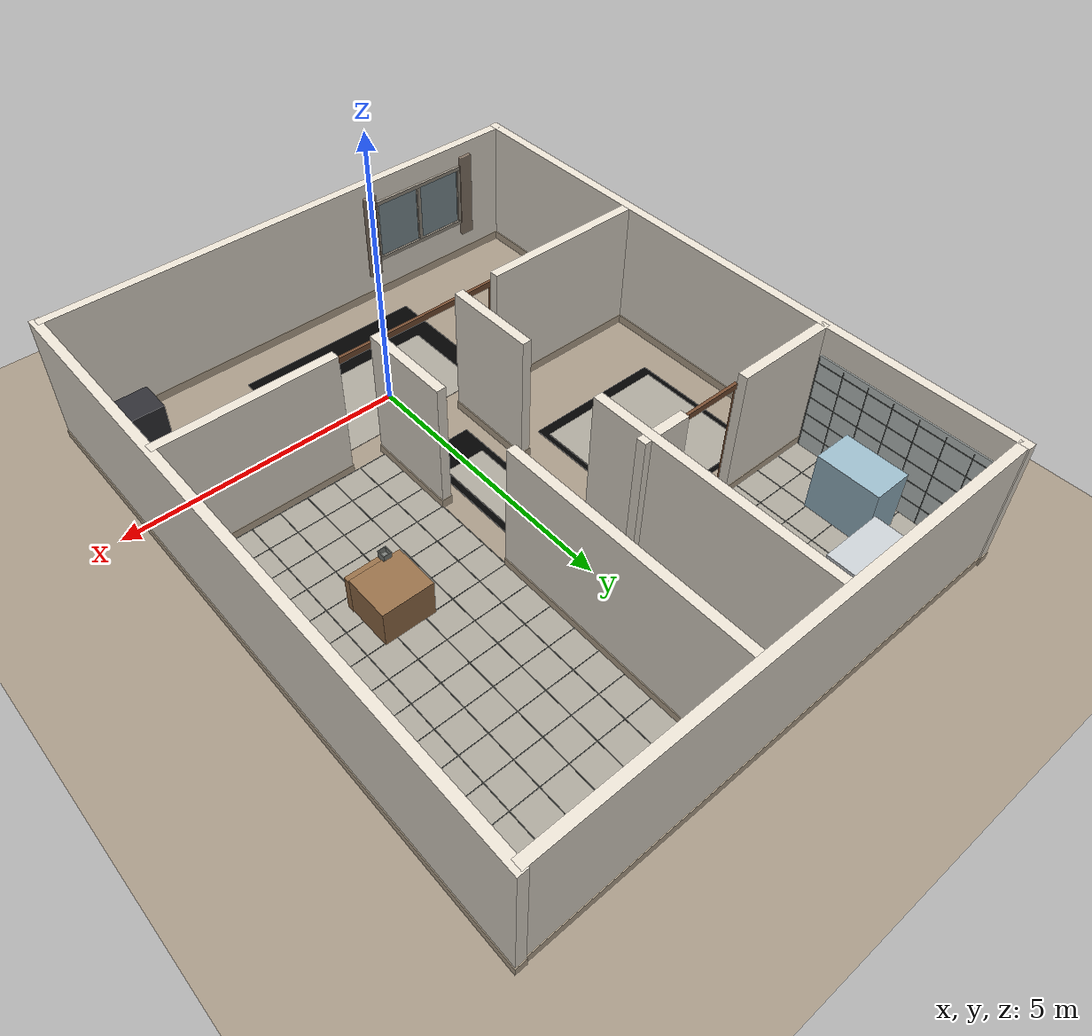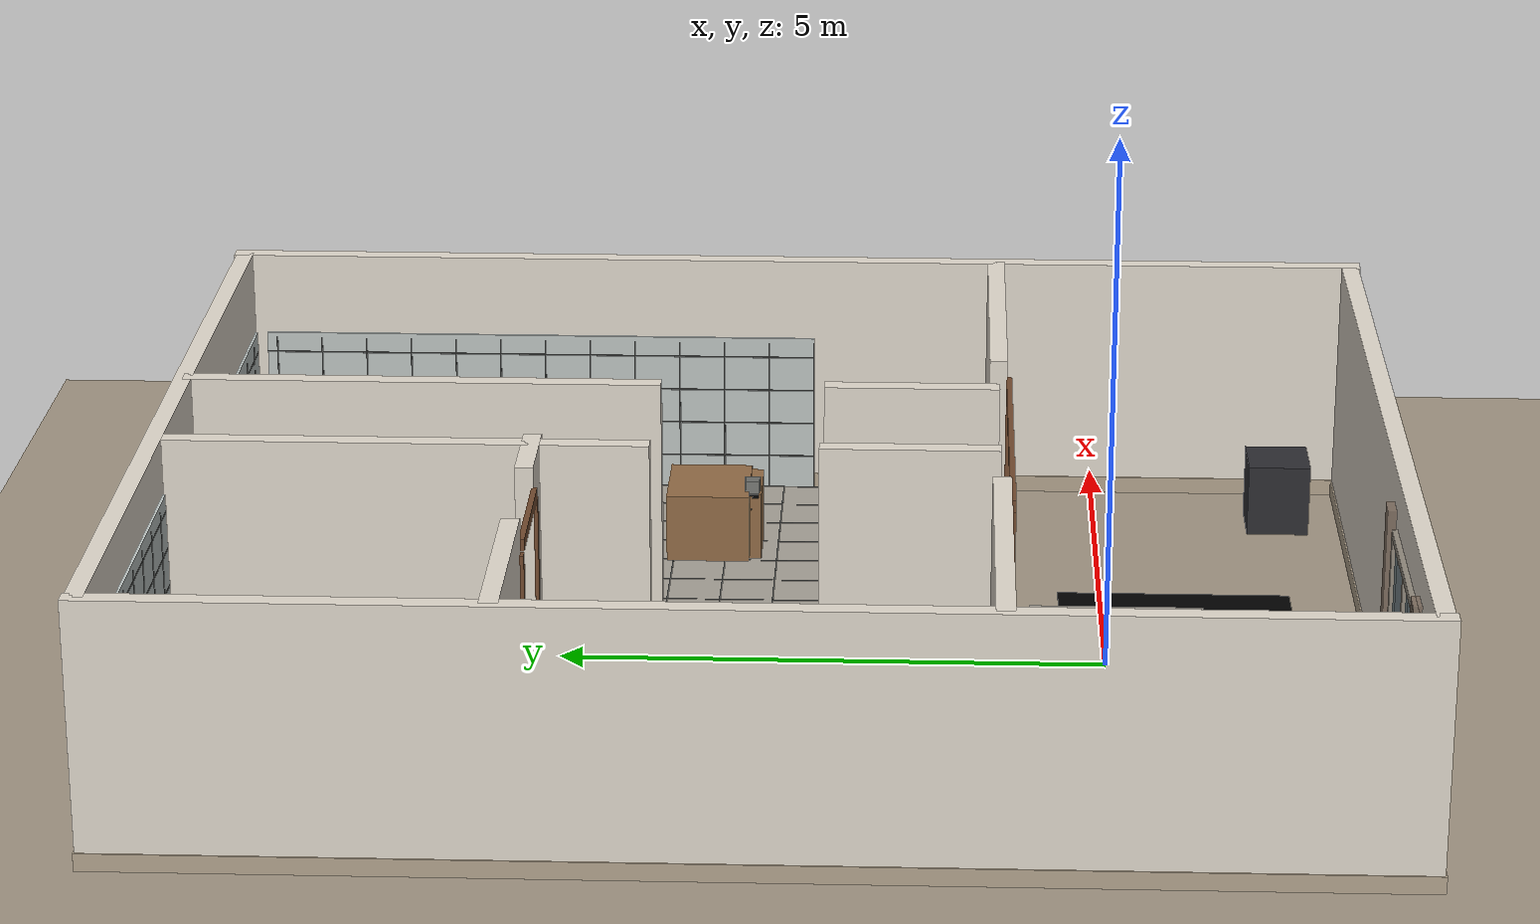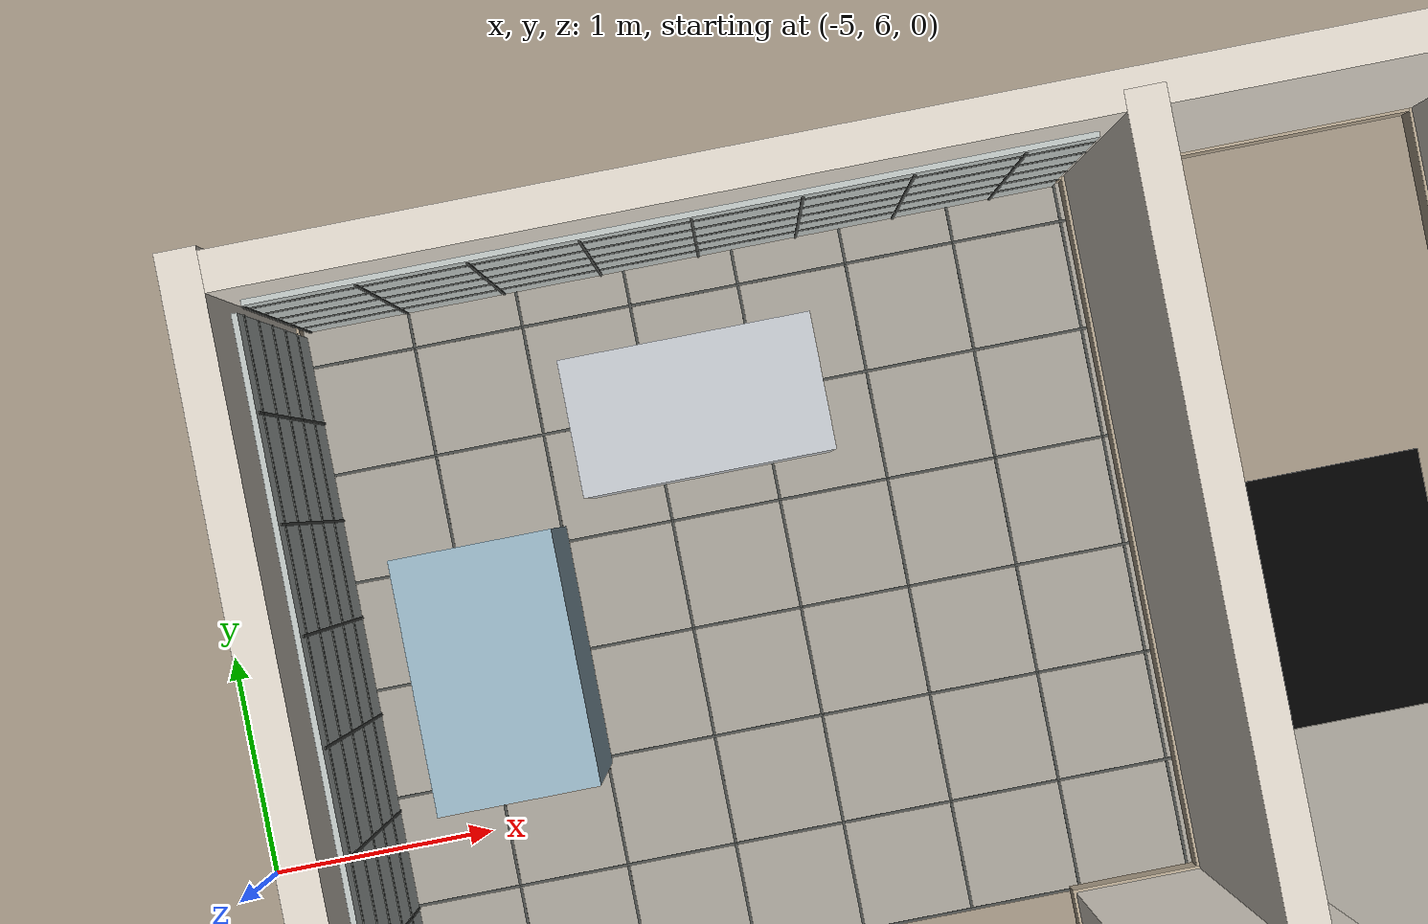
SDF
<sdf version="1.9">
 <world name="tangying_home">
  <physics name="physics" type="ignored">
   <max_step_size>0.002</max_step_size>
   <real_time_factor>1</real_time_factor>
  </physics>
  <gravity>0 0 -9.81</gravity>
  <plugin name="gz::sim::systems::Physics" filename="gz-sim-physics-system"/>
  <plugin name="gz::sim::systems::UserCommands" filename="gz-sim-user-commands-system"/>
  <plugin name="gz::sim::systems::SceneBroadcaster" filename="gz-sim-scene-broadcaster-system"/>
  <plugin name="gz::sim::systems::Imu" filename="gz-sim-imu-system"/>
  <plugin name="gz::sim::systems::Sensors" filename="gz-sim-sensors-system">
   <render_engine>ogre2</render_engine>
  </plugin>
  <light name="sun" type="directional">
   <pose>0 0 10 0 -0 0</pose>
   <diffuse>.85 .85 .85 1</diffuse>
   <specular>.2 .2 .2 1</specular>
   <direction>-.2 -.3 -1</direction>
   <cast_shadows>false</cast_shadows>
  </light>
  <scene><ambient>.5 .5 .5 1</ambient><background>.7 .8 .9 1</background></scene>
  <model name="world_geometry">
   <static>true</static>
   <link name="body">
    <collision name="geom-0">
     <pose>0 3 0 0 -0 0</pose>
     <geometry><plane><normal>0 0 1</normal><size>40 40</size></plane></geometry>
     <surface><friction><ode><mu>1.0</mu><mu2>1.0</mu2></ode></friction></surface>
    </collision>
    <visual name="geom-0">
     <pose>0 3 0 0 -0 0</pose>
     <geometry><plane><normal>0 0 1</normal><size>40 40</size></plane></geometry>
     <material>
      <ambient>0.639999985695 0.589999973774 0.519999980927 1</ambient>
      <diffuse>0.639999985695 0.589999973774 0.519999980927 1</diffuse>
      <pbr>
       <metal>
        <albedo_map>/assets/xlerobot-home/textures/texture-6.png</albedo_map>
        <roughness>0.85</roughness>
        <metalness>0</metalness>
       </metal>
      </pbr>
     </material>
    </visual>
   </link>
  </model>
  <model name="wall_outer_west">
   <pose>-4.5 3 1.2 0 -0 0</pose>
   <static>true</static>
   <link name="body">
    <inertial>
     <pose>0 0 -0.0422056108731 0 -0 0</pose>
     <mass>9059.436224000001</mass>
     <inertia>
      <ixx>99358.00563662639</ixx>
      <iyy>4624.67001646871</iyy>
      <izz>94773.54077546581</izz>
      <ixy>0.0</ixy>
      <ixz>0.0</ixz>
      <iyz>0.0</iyz>
     </inertia>
    </inertial>
    <collision name="geom-46">
     <geometry><box><size>0.16 11.2 2.4</size></box></geometry>
     <surface><friction><ode><mu>1.0</mu><mu2>1.0</mu2></ode></friction></surface>
    </collision>
    <visual name="geom-46">
     <geometry><box><size>0.16 11.2 2.4</size></box></geometry>
     <material>
      <ambient>0.899999976158 0.879999995232 0.839999973774 1</ambient>
      <diffuse>0.899999976158 0.879999995232 0.839999973774 1</diffuse>
     </material>
    </visual>
    <visual name="geom-47">
     <geometry><box><size>0.164 11.204 2.404</size></box></geometry>
     <material>
      <ambient>0.899999976158 0.870000004768 0.819999992847 1</ambient>
      <diffuse>0.899999976158 0.870000004768 0.819999992847 1</diffuse>
     </material>
    </visual>
    <visual name="geom-48">
     <pose>0 0 -1.12 0 -0 0</pose>
     <geometry><box><size>0.19 11.23 0.16</size></box></geometry>
     <material>
      <ambient>0.72000002861 0.660000026226 0.569999992847 1</ambient>
      <diffuse>0.72000002861 0.660000026226 0.569999992847 1</diffuse>
     </material>
    </visual>
   </link>
  </model>
  <model name="wall_outer_east">
   <pose>4.5 3 1.2 0 -0 0</pose>
   <static>true</static>
   <link name="body">
    <inertial>
     <pose>0 0 -0.0422056108731 0 -0 0</pose>
     <mass>9059.436224000001</mass>
     <inertia>
      <ixx>99358.00563662639</ixx>
      <iyy>4624.67001646871</iyy>
      <izz>94773.54077546581</izz>
      <ixy>0.0</ixy>
      <ixz>0.0</ixz>
      <iyz>0.0</iyz>
     </inertia>
    </inertial>
    <collision name="geom-49">
     <geometry><box><size>0.16 11.2 2.4</size></box></geometry>
     <surface><friction><ode><mu>1.0</mu><mu2>1.0</mu2></ode></friction></surface>
    </collision>
    <visual name="geom-49">
     <geometry><box><size>0.16 11.2 2.4</size></box></geometry>
     <material>
      <ambient>0.899999976158 0.879999995232 0.839999973774 1</ambient>
      <diffuse>0.899999976158 0.879999995232 0.839999973774 1</diffuse>
     </material>
    </visual>
    <visual name="geom-50">
     <geometry><box><size>0.164 11.204 2.404</size></box></geometry>
     <material>
      <ambient>0.899999976158 0.870000004768 0.819999992847 1</ambient>
      <diffuse>0.899999976158 0.870000004768 0.819999992847 1</diffuse>
     </material>
    </visual>
    <visual name="geom-51">
     <pose>0 0 -1.12 0 -0 0</pose>
     <geometry><box><size>0.19 11.23 0.16</size></box></geometry>
     <material>
      <ambient>0.72000002861 0.660000026226 0.569999992847 1</ambient>
      <diffuse>0.72000002861 0.660000026226 0.569999992847 1</diffuse>
     </material>
    </visual>
   </link>
  </model>
  <model name="wall_outer_south">
   <pose>0 -2.5 1.2 0 -0 0</pose>
   <static>true</static>
   <link name="body">
    <inertial>
     <pose>0 0 -0.0422303355034 0 -0 0</pose>
     <mass>7280.393024</mass>
     <inertia>
      <ixx>3716.612141078708</ixx>
      <iyy>52876.7876105292</iyy>
      <izz>49192.48564998741</izz>
      <ixy>0.0</ixy>
      <ixz>0.0</ixz>
      <iyz>0.0</iyz>
     </inertia>
    </inertial>
    <collision name="geom-52">
     <geometry><box><size>9 0.16 2.4</size></box></geometry>
     <surface><friction><ode><mu>1.0</mu><mu2>1.0</mu2></ode></friction></surface>
    </collision>
    <visual name="geom-52">
     <geometry><box><size>9 0.16 2.4</size></box></geometry>
     <material>
      <ambient>0.899999976158 0.879999995232 0.839999973774 1</ambient>
      <diffuse>0.899999976158 0.879999995232 0.839999973774 1</diffuse>
     </material>
    </visual>
    <visual name="geom-53">
     <geometry><box><size>9.004 0.164 2.404</size></box></geometry>
     <material>
      <ambient>0.899999976158 0.870000004768 0.819999992847 1</ambient>
      <diffuse>0.899999976158 0.870000004768 0.819999992847 1</diffuse>
     </material>
    </visual>
    <visual name="geom-54">
     <pose>0 0 -1.12 0 -0 0</pose>
     <geometry><box><size>9.03 0.19 0.16</size></box></geometry>
     <material>
      <ambient>0.72000002861 0.660000026226 0.569999992847 1</ambient>
      <diffuse>0.72000002861 0.660000026226 0.569999992847 1</diffuse>
     </material>
    </visual>
   </link>
  </model>
  <model name="wall_outer_north">
   <pose>0 8.5 1.2 0 -0 0</pose>
   <static>true</static>
   <link name="body">
    <inertial>
     <pose>0 0 -0.0422303355034 0 -0 0</pose>
     <mass>7280.393024</mass>
     <inertia>
      <ixx>3716.612141078708</ixx>
      <iyy>52876.7876105292</iyy>
      <izz>49192.48564998741</izz>
      <ixy>0.0</ixy>
      <ixz>0.0</ixz>
      <iyz>0.0</iyz>
     </inertia>
    </inertial>
    <collision name="geom-55">
     <geometry><box><size>9 0.16 2.4</size></box></geometry>
     <surface><friction><ode><mu>1.0</mu><mu2>1.0</mu2></ode></friction></surface>
    </collision>
    <visual name="geom-55">
     <geometry><box><size>9 0.16 2.4</size></box></geometry>
     <material>
      <ambient>0.899999976158 0.879999995232 0.839999973774 1</ambient>
      <diffuse>0.899999976158 0.879999995232 0.839999973774 1</diffuse>
     </material>
    </visual>
    <visual name="geom-56">
     <geometry><box><size>9.004 0.164 2.404</size></box></geometry>
     <material>
      <ambient>0.899999976158 0.870000004768 0.819999992847 1</ambient>
      <diffuse>0.899999976158 0.870000004768 0.819999992847 1</diffuse>
     </material>
    </visual>
    <visual name="geom-57">
     <pose>0 0 -1.12 0 -0 0</pose>
     <geometry><box><size>9.03 0.19 0.16</size></box></geometry>
     <material>
      <ambient>0.72000002861 0.660000026226 0.569999992847 1</ambient>
      <diffuse>0.72000002861 0.660000026226 0.569999992847 1</diffuse>
     </material>
    </visual>
   </link>
  </model>
  <model name="wall_living_west">
   <pose>-3 1 1.2 0 -0 0</pose>
   <static>true</static>
   <link name="body">
    <inertial>
     <pose>0 0 -0.0424818882856 0 -0 0</pose>
     <mass>2428.4570240000003</mass>
     <inertia>
      <ixx>1240.0904939685474</ixx>
      <iyy>3059.8029039627963</iyy>
      <izz>1830.490841155167</izz>
      <ixy>0.0</ixy>
      <ixz>0.0</ixz>
      <iyz>0.0</iyz>
     </inertia>
    </inertial>
    <collision name="geom-58">
     <geometry><box><size>3 0.16 2.4</size></box></geometry>
     <surface><friction><ode><mu>1.0</mu><mu2>1.0</mu2></ode></friction></surface>
    </collision>
    <visual name="geom-58">
     <geometry><box><size>3 0.16 2.4</size></box></geometry>
     <material>
      <ambient>0.879999995232 0.819999992847 0.740000009537 1</ambient>
      <diffuse>0.879999995232 0.819999992847 0.740000009537 1</diffuse>
     </material>
    </visual>
    <visual name="geom-59">
     <geometry><box><size>3.004 0.164 2.404</size></box></geometry>
     <material>
      <ambient>0.899999976158 0.870000004768 0.819999992847 1</ambient>
      <diffuse>0.899999976158 0.870000004768 0.819999992847 1</diffuse>
     </material>
    </visual>
    <visual name="geom-60">
     <pose>0 0 -1.12 0 -0 0</pose>
     <geometry><box><size>3.03 0.19 0.16</size></box></geometry>
     <material>
      <ambient>0.72000002861 0.660000026226 0.569999992847 1</ambient>
      <diffuse>0.72000002861 0.660000026226 0.569999992847 1</diffuse>
     </material>
    </visual>
   </link>
  </model>
  <model name="wall_living_east">
   <pose>3 1 1.2 0 -0 0</pose>
   <static>true</static>
   <link name="body">
    <inertial>
     <pose>0 0 -0.0424818882856 0 -0 0</pose>
     <mass>2428.4570240000003</mass>
     <inertia>
      <ixx>1240.0904939685474</ixx>
      <iyy>3059.8029039627963</iyy>
      <izz>1830.490841155167</izz>
      <ixy>0.0</ixy>
      <ixz>0.0</ixz>
      <iyz>0.0</iyz>
     </inertia>
    </inertial>
    <collision name="geom-61">
     <geometry><box><size>3 0.16 2.4</size></box></geometry>
     <surface><friction><ode><mu>1.0</mu><mu2>1.0</mu2></ode></friction></surface>
    </collision>
    <visual name="geom-61">
     <geometry><box><size>3 0.16 2.4</size></box></geometry>
     <material>
      <ambient>0.879999995232 0.819999992847 0.740000009537 1</ambient>
      <diffuse>0.879999995232 0.819999992847 0.740000009537 1</diffuse>
     </material>
    </visual>
    <visual name="geom-62">
     <geometry><box><size>3.004 0.164 2.404</size></box></geometry>
     <material>
      <ambient>0.899999976158 0.870000004768 0.819999992847 1</ambient>
      <diffuse>0.899999976158 0.870000004768 0.819999992847 1</diffuse>
     </material>
    </visual>
    <visual name="geom-63">
     <pose>0 0 -1.12 0 -0 0</pose>
     <geometry><box><size>3.03 0.19 0.16</size></box></geometry>
     <material>
      <ambient>0.72000002861 0.660000026226 0.569999992847 1</ambient>
      <diffuse>0.72000002861 0.660000026226 0.569999992847 1</diffuse>
     </material>
    </visual>
   </link>
  </model>
  <model name="wall_corridor_kitchen_south">
   <pose>0.8 1.8 1.2 0 -0 0</pose>
   <static>true</static>
   <link name="body">
    <inertial>
     <pose>0 0 -0.0428115300837 0 -0 0</pose>
     <mass>1296.3386239999998</mass>
     <inertia>
      <ixx>936.9857775636466</ixx>
      <iyy>662.2351946158064</iyy>
      <izz>280.50493925435734</izz>
      <ixy>0.0</ixy>
      <ixz>0.0</ixz>
      <iyz>0.0</iyz>
     </inertia>
    </inertial>
    <collision name="geom-64">
     <geometry><box><size>0.16 1.6 2.4</size></box></geometry>
     <surface><friction><ode><mu>1.0</mu><mu2>1.0</mu2></ode></friction></surface>
    </collision>
    <visual name="geom-64">
     <geometry><box><size>0.16 1.6 2.4</size></box></geometry>
     <material>
      <ambient>0.879999995232 0.819999992847 0.740000009537 1</ambient>
      <diffuse>0.879999995232 0.819999992847 0.740000009537 1</diffuse>
     </material>
    </visual>
    <visual name="geom-65">
     <geometry><box><size>0.164 1.604 2.404</size></box></geometry>
     <material>
      <ambient>0.899999976158 0.870000004768 0.819999992847 1</ambient>
      <diffuse>0.899999976158 0.870000004768 0.819999992847 1</diffuse>
     </material>
    </visual>
    <visual name="geom-66">
     <pose>0 0 -1.12 0 -0 0</pose>
     <geometry><box><size>0.19 1.63 0.16</size></box></geometry>
     <material>
      <ambient>0.72000002861 0.660000026226 0.569999992847 1</ambient>
      <diffuse>0.72000002861 0.660000026226 0.569999992847 1</diffuse>
     </material>
    </visual>
   </link>
  </model>
  <model name="wall_corridor_kitchen_north">
   <pose>0.8 6.3 1.2 0 -0 0</pose>
   <static>true</static>
   <link name="body">
    <inertial>
     <pose>0 0 -0.0423618718995 0 -0 0</pose>
     <mass>3560.575424</mass>
     <inertia>
      <ixx>7562.507721730673</ixx>
      <iyy>1817.945601170019</iyy>
      <izz>5760.3646265759735</izz>
      <ixy>0.0</ixy>
      <ixz>0.0</ixz>
      <iyz>0.0</iyz>
     </inertia>
    </inertial>
    <collision name="geom-67">
     <geometry><box><size>0.16 4.4 2.4</size></box></geometry>
     <surface><friction><ode><mu>1.0</mu><mu2>1.0</mu2></ode></friction></surface>
    </collision>
    <visual name="geom-67">
     <geometry><box><size>0.16 4.4 2.4</size></box></geometry>
     <material>
      <ambient>0.879999995232 0.819999992847 0.740000009537 1</ambient>
      <diffuse>0.879999995232 0.819999992847 0.740000009537 1</diffuse>
     </material>
    </visual>
    <visual name="geom-68">
     <geometry><box><size>0.164 4.404 2.404</size></box></geometry>
     <material>
      <ambient>0.899999976158 0.870000004768 0.819999992847 1</ambient>
      <diffuse>0.899999976158 0.870000004768 0.819999992847 1</diffuse>
     </material>
    </visual>
    <visual name="geom-69">
     <pose>0 0 -1.12 0 -0 0</pose>
     <geometry><box><size>0.19 4.43 0.16</size></box></geometry>
     <material>
      <ambient>0.72000002861 0.660000026226 0.569999992847 1</ambient>
      <diffuse>0.72000002861 0.660000026226 0.569999992847 1</diffuse>
     </material>
    </visual>
   </link>
  </model>
  <model name="wall_corridor_bed_south">
   <pose>-0.8 1.8 1.2 0 -0 0</pose>
   <static>true</static>
   <link name="body">
    <inertial>
     <pose>0 0 -0.0428115300837 0 -0 0</pose>
     <mass>1296.3386239999998</mass>
     <inertia>
      <ixx>936.9857775636466</ixx>
      <iyy>662.2351946158064</iyy>
      <izz>280.50493925435734</izz>
      <ixy>0.0</ixy>
      <ixz>0.0</ixz>
      <iyz>0.0</iyz>
     </inertia>
    </inertial>
    <collision name="geom-70">
     <geometry><box><size>0.16 1.6 2.4</size></box></geometry>
     <surface><friction><ode><mu>1.0</mu><mu2>1.0</mu2></ode></friction></surface>
    </collision>
    <visual name="geom-70">
     <geometry><box><size>0.16 1.6 2.4</size></box></geometry>
     <material>
      <ambient>0.879999995232 0.819999992847 0.740000009537 1</ambient>
      <diffuse>0.879999995232 0.819999992847 0.740000009537 1</diffuse>
     </material>
    </visual>
    <visual name="geom-71">
     <geometry><box><size>0.164 1.604 2.404</size></box></geometry>
     <material>
      <ambient>0.899999976158 0.870000004768 0.819999992847 1</ambient>
      <diffuse>0.899999976158 0.870000004768 0.819999992847 1</diffuse>
     </material>
    </visual>
    <visual name="geom-72">
     <pose>0 0 -1.12 0 -0 0</pose>
     <geometry><box><size>0.19 1.63 0.16</size></box></geometry>
     <material>
      <ambient>0.72000002861 0.660000026226 0.569999992847 1</ambient>
      <diffuse>0.72000002861 0.660000026226 0.569999992847 1</diffuse>
     </material>
    </visual>
   </link>
  </model>
  <model name="wall_corridor_bed_north">
   <pose>-0.8 6.3 1.2 0 -0 0</pose>
   <static>true</static>
   <link name="body">
    <inertial>
     <pose>0 0 -0.0423618718995 0 -0 0</pose>
     <mass>3560.575424</mass>
     <inertia>
      <ixx>7562.507721730673</ixx>
      <iyy>1817.945601170019</iyy>
      <izz>5760.3646265759735</izz>
      <ixy>0.0</ixy>
      <ixz>0.0</ixz>
      <iyz>0.0</iyz>
     </inertia>
    </inertial>
    <collision name="geom-73">
     <geometry><box><size>0.16 4.4 2.4</size></box></geometry>
     <surface><friction><ode><mu>1.0</mu><mu2>1.0</mu2></ode></friction></surface>
    </collision>
    <visual name="geom-73">
     <geometry><box><size>0.16 4.4 2.4</size></box></geometry>
     <material>
      <ambient>0.879999995232 0.819999992847 0.740000009537 1</ambient>
      <diffuse>0.879999995232 0.819999992847 0.740000009537 1</diffuse>
     </material>
    </visual>
    <visual name="geom-74">
     <geometry><box><size>0.164 4.404 2.404</size></box></geometry>
     <material>
      <ambient>0.899999976158 0.870000004768 0.819999992847 1</ambient>
      <diffuse>0.899999976158 0.870000004768 0.819999992847 1</diffuse>
     </material>
    </visual>
    <visual name="geom-75">
     <pose>0 0 -1.12 0 -0 0</pose>
     <geometry><box><size>0.19 4.43 0.16</size></box></geometry>
     <material>
      <ambient>0.72000002861 0.660000026226 0.569999992847 1</ambient>
      <diffuse>0.72000002861 0.660000026226 0.569999992847 1</diffuse>
     </material>
    </visual>
   </link>
  </model>
  <model name="wall_bed_bath">
   <pose>-3.575 5.15 1.2 0 -0 0</pose>
   <static>true</static>
   <link name="body">
    <inertial>
     <pose>0 0 -0.0427161347433 0 -0 0</pose>
     <mass>1498.5026240000002</mass>
     <inertia>
      <ixx>765.4236744143673</ixx>
      <iyy>1190.9187768062086</iyy>
      <izz>432.14661492235854</izz>
      <ixy>0.0</ixy>
      <ixz>0.0</ixz>
      <iyz>0.0</iyz>
     </inertia>
    </inertial>
    <collision name="geom-76">
     <geometry><box><size>1.85 0.16 2.4</size></box></geometry>
     <surface><friction><ode><mu>1.0</mu><mu2>1.0</mu2></ode></friction></surface>
    </collision>
    <visual name="geom-76">
     <geometry><box><size>1.85 0.16 2.4</size></box></geometry>
     <material>
      <ambient>0.879999995232 0.819999992847 0.740000009537 1</ambient>
      <diffuse>0.879999995232 0.819999992847 0.740000009537 1</diffuse>
     </material>
    </visual>
    <visual name="geom-77">
     <geometry><box><size>1.854 0.164 2.404</size></box></geometry>
     <material>
      <ambient>0.899999976158 0.870000004768 0.819999992847 1</ambient>
      <diffuse>0.899999976158 0.870000004768 0.819999992847 1</diffuse>
     </material>
    </visual>
    <visual name="geom-78">
     <pose>0 0 -1.12 0 -0 0</pose>
     <geometry><box><size>1.88 0.19 0.16</size></box></geometry>
     <material>
      <ambient>0.72000002861 0.660000026226 0.569999992847 1</ambient>
      <diffuse>0.72000002861 0.660000026226 0.569999992847 1</diffuse>
     </material>
    </visual>
   </link>
  </model>
  <model name="wall_bed_bath_east">
   <pose>-1.025 5.15 1.2 0 -0 0</pose>
   <static>true</static>
   <link name="body">
    <inertial>
     <pose>0 0 -0.0434331907378 0 -0 0</pose>
     <mass>689.846624</mass>
     <inertia>
      <ixx>352.66944771030734</ixx>
      <iyy>392.9794643261474</iyy>
      <izz>43.37290425035744</izz>
      <ixy>0.0</ixy>
      <ixz>0.0</ixz>
      <iyz>0.0</iyz>
     </inertia>
    </inertial>
    <collision name="geom-79">
     <geometry><box><size>0.85 0.16 2.4</size></box></geometry>
     <surface><friction><ode><mu>1.0</mu><mu2>1.0</mu2></ode></friction></surface>
    </collision>
    <visual name="geom-79">
     <geometry><box><size>0.85 0.16 2.4</size></box></geometry>
     <material>
      <ambient>0.879999995232 0.819999992847 0.740000009537 1</ambient>
      <diffuse>0.879999995232 0.819999992847 0.740000009537 1</diffuse>
     </material>
    </visual>
    <visual name="geom-80">
     <geometry><box><size>0.854 0.164 2.404</size></box></geometry>
     <material>
      <ambient>0.899999976158 0.870000004768 0.819999992847 1</ambient>
      <diffuse>0.899999976158 0.870000004768 0.819999992847 1</diffuse>
     </material>
    </visual>
    <visual name="geom-81">
     <pose>0 0 -1.12 0 -0 0</pose>
     <geometry><box><size>0.88 0.19 0.16</size></box></geometry>
     <material>
      <ambient>0.72000002861 0.660000026226 0.569999992847 1</ambient>
      <diffuse>0.72000002861 0.660000026226 0.569999992847 1</diffuse>
     </material>
    </visual>
   </link>
  </model>
  <model name="living_room">
   <pose>0 -0.7 0.006 0 -0 0</pose>
   <static>true</static>
   <link name="body">
    <inertial>
     <mass>74.80000000000001</mass>
     <inertia>
      <ixx>30.169956666666675</ixx>
      <iyy>72.05795666666667</iyy>
      <izz>102.22666666666667</izz>
      <ixy>0.0</ixy>
      <ixz>0.0</ixz>
      <iyz>0.0</iyz>
     </inertia>
    </inertial>
    <visual name="geom-82">
     <geometry><box><size>3.4 2.2 0.01</size></box></geometry>
     <material><ambient>0 0 0 0</ambient><diffuse>0 0 0 0</diffuse></material>
    </visual>
   </link>
  </model>
  <model name="home_corridor">
   <pose>0 4.2 0.006 0 -0 0</pose>
   <static>true</static>
   <link name="body">
    <inertial>
     <mass>51.84</mass>
     <inertia>
      <ixx>125.97163200000001</ixx>
      <iyy>3.9817440000000004</iyy>
      <izz>129.95251200000004</izz>
      <ixy>0.0</ixy>
      <ixz>0.0</ixz>
      <iyz>0.0</iyz>
     </inertia>
    </inertial>
    <visual name="geom-83">
     <geometry><box><size>0.96 5.4 0.01</size></box></geometry>
     <material><ambient>0 0 0 0</ambient><diffuse>0 0 0 0</diffuse></material>
    </visual>
   </link>
  </model>
  <model name="kitchen">
   <pose>2.5 4.7 0.006 0 -0 0</pose>
   <static>true</static>
   <link name="body">
    <inertial>
     <mass>75.0</mass>
     <inertia>
      <ixx>56.25062499999999</ixx>
      <iyy>39.063125</iyy>
      <izz>95.3125</izz>
      <ixy>0.0</ixy>
      <ixz>0.0</ixz>
      <iyz>0.0</iyz>
     </inertia>
    </inertial>
    <visual name="geom-84">
     <geometry><box><size>2.5 3 0.01</size></box></geometry>
     <material><ambient>0 0 0 0</ambient><diffuse>0 0 0 0</diffuse></material>
    </visual>
   </link>
  </model>
  <model name="bedroom">
   <pose>-2.6 3.55 0.006 0 -0 0</pose>
   <static>true</static>
   <link name="body">
    <inertial>
     <mass>62.5</mass>
     <inertia>
      <ixx>32.55260416666666</ixx>
      <iyy>32.55260416666666</iyy>
      <izz>65.10416666666667</izz>
      <ixy>0.0</ixy>
      <ixz>0.0</ixz>
      <iyz>0.0</iyz>
     </inertia>
    </inertial>
    <visual name="geom-85">
     <geometry><box><size>2.5 2.5 0.01</size></box></geometry>
     <material><ambient>0 0 0 0</ambient><diffuse>0 0 0 0</diffuse></material>
    </visual>
   </link>
  </model>
  <model name="bathroom">
   <pose>-2.6 6.85 0.006 0 -0 0</pose>
   <static>true</static>
   <link name="body">
    <inertial>
     <mass>67.5</mass>
     <inertia>
      <ixx>41.0068125</ixx>
      <iyy>35.1568125</iyy>
      <izz>76.16250000000001</izz>
      <ixy>0.0</ixy>
      <ixz>0.0</ixz>
      <iyz>0.0</iyz>
     </inertia>
    </inertial>
    <visual name="geom-86">
     <geometry><box><size>2.5 2.7 0.01</size></box></geometry>
     <material><ambient>0 0 0 0</ambient><diffuse>0 0 0 0</diffuse></material>
    </visual>
   </link>
  </model>
  <model name="living_rug">
   <pose>0 -0.15 0.012 0 -0 0</pose>
   <static>true</static>
   <link name="body">
    <inertial>
     <mass>53.136</mass>
     <inertia>
      <ixx>11.910186431999998</ixx>
      <iyy>32.280757632000004</iyy>
      <izz>44.189668800000014</izz>
      <ixy>0.0</ixy>
      <ixz>0.0</ixz>
      <iyz>0.0</iyz>
     </inertia>
    </inertial>
    <visual name="geom-87">
     <geometry><box><size>2.7 1.64 0.012</size></box></geometry>
     <material>
      <ambient>0.660000026226 0.639999985695 0.600000023842 1</ambient>
      <diffuse>0.660000026226 0.639999985695 0.600000023842 1</diffuse>
      <pbr>
       <metal>
        <albedo_map>/assets/xlerobot-home/textures/texture-7.png</albedo_map>
        <roughness>0.85</roughness>
        <metalness>0</metalness>
       </metal>
      </pbr>
     </material>
    </visual>
   </link>
  </model>
  <model name="corridor_runner">
   <pose>0 3.9 0.012 0 -0 0</pose>
   <static>true</static>
   <link name="body">
    <inertial>
     <mass>31.968000000000004</mass>
     <inertia>
      <ixx>36.47054361600001</ixx>
      <iyy>1.3814012160000002</iyy>
      <izz>37.85117760000001</izz>
      <ixy>0.0</ixy>
      <ixz>0.0</ixz>
      <iyz>0.0</iyz>
     </inertia>
    </inertial>
    <visual name="geom-88">
     <geometry><box><size>0.72 3.7 0.012</size></box></geometry>
     <material>
      <ambient>0.660000026226 0.639999985695 0.600000023842 1</ambient>
      <diffuse>0.660000026226 0.639999985695 0.600000023842 1</diffuse>
      <pbr>
       <metal>
        <albedo_map>/assets/xlerobot-home/textures/texture-7.png</albedo_map>
        <roughness>0.85</roughness>
        <metalness>0</metalness>
       </metal>
      </pbr>
     </material>
    </visual>
   </link>
  </model>
  <model name="kitchen_tiles">
   <pose>2.65 4.75 0.012 0 -0 0</pose>
   <static>true</static>
   <link name="body">
    <inertial>
     <mass>310.104</mass>
     <inertia>
      <ixx>1377.1239012479998</ixx>
      <iyy>323.84532844800003</iyy>
      <izz>1700.9617872</izz>
      <ixy>0.0</ixy>
      <ixz>0.0</ixz>
      <iyz>0.0</iyz>
     </inertia>
    </inertial>
    <visual name="geom-89">
     <geometry><box><size>3.54 7.3 0.012</size></box></geometry>
     <material>
      <ambient>0.660000026226 0.639999985695 0.600000023842 1</ambient>
      <diffuse>0.660000026226 0.639999985695 0.600000023842 1</diffuse>
      <pbr>
       <metal>
        <albedo_map>/assets/xlerobot-home/textures/texture-7.png</albedo_map>
        <roughness>0.85</roughness>
        <metalness>0</metalness>
       </metal>
      </pbr>
     </material>
    </visual>
   </link>
  </model>
  <model name="bedroom_rug">
   <pose>-2.6 3.6 0.012 0 -0 0</pose>
   <static>true</static>
   <link name="body">
    <inertial>
     <mass>61.824000000000005</mass>
     <inertia>
      <ixx>25.851417088000005</ixx>
      <iyy>27.254821887999995</iyy>
      <izz>53.10475520000001</izz>
      <ixy>0.0</ixy>
      <ixz>0.0</ixz>
      <iyz>0.0</iyz>
     </inertia>
    </inertial>
    <visual name="geom-90">
     <geometry><box><size>2.3 2.24 0.012</size></box></geometry>
     <material>
      <ambient>0.660000026226 0.639999985695 0.600000023842 1</ambient>
      <diffuse>0.660000026226 0.639999985695 0.600000023842 1</diffuse>
      <pbr>
       <metal>
        <albedo_map>/assets/xlerobot-home/textures/texture-7.png</albedo_map>
        <roughness>0.85</roughness>
        <metalness>0</metalness>
       </metal>
      </pbr>
     </material>
    </visual>
   </link>
  </model>
  <model name="bathroom_tiles">
   <pose>-2.65 6.825 0.012 0 -0 0</pose>
   <static>true</static>
   <link name="body">
    <inertial>
     <mass>135.93600000000004</mass>
     <inertia>
      <ixx>116.00035123200006</ixx>
      <iyy>141.95959603200006</iyy>
      <izz>257.9566848000001</izz>
      <ixy>0.0</ixy>
      <ixz>0.0</ixz>
      <iyz>0.0</iyz>
     </inertia>
    </inertial>
    <visual name="geom-91">
     <geometry><box><size>3.54 3.2 0.012</size></box></geometry>
     <material>
      <ambient>0.660000026226 0.639999985695 0.600000023842 1</ambient>
      <diffuse>0.660000026226 0.639999985695 0.600000023842 1</diffuse>
      <pbr>
       <metal>
        <albedo_map>/assets/xlerobot-home/textures/texture-7.png</albedo_map>
        <roughness>0.85</roughness>
        <metalness>0</metalness>
       </metal>
      </pbr>
     </material>
    </visual>
   </link>
  </model>
  <model name="bathroom_sink">
   <pose>-2.7 7.7 0.45 0 -0 0</pose>
   <static>true</static>
   <link name="body">
    <inertial>
     <mass>594.0000000000001</mass>
     <inertia>
      <ixx>57.91500000000001</ixx>
      <iyy>99.99000000000005</iyy>
      <izz>77.71500000000003</izz>
      <ixy>0.0</ixy>
      <ixz>0.0</ixz>
      <iyz>0.0</iyz>
     </inertia>
    </inertial>
    <collision name="geom-102">
     <geometry><box><size>1.1 0.6 0.9</size></box></geometry>
     <surface><friction><ode><mu>1.0</mu><mu2>1.0</mu2></ode></friction></surface>
    </collision>
    <visual name="geom-102">
     <geometry><box><size>1.1 0.6 0.9</size></box></geometry>
     <material>
      <ambient>0.77999997139 0.800000011921 0.819999992847 1</ambient>
      <diffuse>0.77999997139 0.800000011921 0.819999992847 1</diffuse>
     </material>
    </visual>
   </link>
  </model>
  <model name="bathroom_shower">
   <pose>-3.75 6.75 0.55 0 -0 0</pose>
   <static>true</static>
   <link name="body">
    <inertial>
     <mass>847.0000000000001</mass>
     <inertia>
      <ixx>170.81166666666672</ixx>
      <iyy>119.99166666666669</iyy>
      <izz>119.99166666666669</izz>
      <ixy>0.0</ixy>
      <ixz>0.0</ixz>
      <iyz>0.0</iyz>
     </inertia>
    </inertial>
    <collision name="geom-103">
     <geometry><box><size>0.7 1.1 1.1</size></box></geometry>
     <surface><friction><ode><mu>1.0</mu><mu2>1.0</mu2></ode></friction></surface>
    </collision>
    <visual name="geom-103">
     <geometry><box><size>0.7 1.1 1.1</size></box></geometry>
     <material>
      <ambient>0.600000023842 0.72000002861 0.77999997139 1</ambient>
      <diffuse>0.600000023842 0.72000002861 0.77999997139 1</diffuse>
     </material>
    </visual>
   </link>
  </model>
  <model name="front_tray">
   <pose>3.6 -1.8 0.35 0 -0 0</pose>
   <static>true</static>
   <link name="body">
    <inertial>
     <mass>252.0</mass>
     <inertia>
      <ixx>17.849999999999998</ixx>
      <iyy>17.849999999999998</iyy>
      <izz>15.12</izz>
      <ixy>0.0</ixy>
      <ixz>0.0</ixz>
      <iyz>0.0</iyz>
     </inertia>
    </inertial>
    <collision name="geom-104">
     <geometry><box><size>0.6 0.6 0.7</size></box></geometry>
     <surface><friction><ode><mu>1.0</mu><mu2>1.0</mu2></ode></friction></surface>
    </collision>
    <visual name="geom-104">
     <geometry><box><size>0.6 0.6 0.7</size></box></geometry>
     <material>
      <ambient>0.180000007153 0.180000007153 0.20000000298 1</ambient>
      <diffuse>0.180000007153 0.180000007153 0.20000000298 1</diffuse>
     </material>
    </visual>
   </link>
  </model>
  <model name="home_task_table">
   <pose>2.6625 3.76 0.4 0 -0 0</pose>
   <static>true</static>
   <link name="body">
    <inertial>
     <pose>0.00937964457856 -0.0524855761563 -0.00439009829094 0 -0 0</pose>
     <mass>517.1837759279829</mass>
     <inertia>
      <ixx>53.262168987537436</ixx>
      <iyy>50.88755423400677</iyy>
      <izz>66.56611024397859</izz>
      <ixy>1.9283424164576104</ixy>
      <ixz>0.17274462609394747</ixz>
      <iyz>-0.8997685256664112</iyz>
     </inertia>
    </inertial>
    <collision name="geom-105">
     <geometry><box><size>0.875 0.79 0.66</size></box></geometry>
     <surface><friction><ode><mu>1.0</mu><mu2>1.0</mu2></ode></friction></surface>
    </collision>
    <visual name="geom-105">
     <geometry><box><size>0.875 0.79 0.66</size></box></geometry>
     <material>
      <ambient>0.579999983311 0.430000007153 0.280000001192 1</ambient>
      <diffuse>0.579999983311 0.430000007153 0.280000001192 1</diffuse>
      <pbr>
       <metal>
        <albedo_map>/assets/xlerobot-home/textures/texture-2.png</albedo_map>
        <roughness>0.85</roughness>
        <metalness>0</metalness>
       </metal>
      </pbr>
     </material>
    </visual>
    <collision name="geom-106">
     <pose>0.0875 -0.45 -0.04 0 -0 0</pose>
     <geometry><box><size>0.7 0.12 0.66</size></box></geometry>
     <surface><friction><ode><mu>1.0</mu><mu2>1.0</mu2></ode></friction></surface>
    </collision>
    <visual name="geom-106">
     <pose>0.0875 -0.45 -0.04 0 -0 0</pose>
     <geometry><box><size>0.7 0.12 0.66</size></box></geometry>
     <material>
      <ambient>0.579999983311 0.430000007153 0.280000001192 1</ambient>
      <diffuse>0.579999983311 0.430000007153 0.280000001192 1</diffuse>
      <pbr>
       <metal>
        <albedo_map>/assets/xlerobot-home/textures/texture-2.png</albedo_map>
        <roughness>0.85</roughness>
        <metalness>0</metalness>
       </metal>
      </pbr>
     </material>
    </visual>
    <visual name="geom-107">
     <pose>-0.29 -0.398 -0.01 0 -0 0</pose>
     <geometry><box><size>0.278 0.012 0.55</size></box></geometry>
     <material>
      <ambient>0.589999973774 0.519999980927 0.409999996424 1</ambient>
      <diffuse>0.589999973774 0.519999980927 0.409999996424 1</diffuse>
     </material>
    </visual>
    <visual name="geom-108">
     <pose>-0.29 -0.413 0.15 0 -1.57079632679 0</pose>
     <geometry><capsule><radius>0.004</radius><length>0.08999999999999997</length></capsule></geometry>
     <material>
      <ambient>0.340000003576 0.34999999404 0.340000003576 1</ambient>
      <diffuse>0.340000003576 0.34999999404 0.340000003576 1</diffuse>
     </material>
    </visual>
    <visual name="geom-109">
     <pose>0 -0.398 -0.01 0 -0 0</pose>
     <geometry><box><size>0.278 0.012 0.55</size></box></geometry>
     <material>
      <ambient>0.589999973774 0.519999980927 0.409999996424 1</ambient>
      <diffuse>0.589999973774 0.519999980927 0.409999996424 1</diffuse>
     </material>
    </visual>
    <visual name="geom-110">
     <pose>0 -0.413 0.15 0 -1.57079632679 0</pose>
     <geometry><capsule><radius>0.004</radius><length>0.09</length></capsule></geometry>
     <material>
      <ambient>0.340000003576 0.34999999404 0.340000003576 1</ambient>
      <diffuse>0.340000003576 0.34999999404 0.340000003576 1</diffuse>
     </material>
    </visual>
    <visual name="geom-111">
     <pose>0.29 -0.398 -0.01 0 -0 0</pose>
     <geometry><box><size>0.278 0.012 0.55</size></box></geometry>
     <material>
      <ambient>0.589999973774 0.519999980927 0.409999996424 1</ambient>
      <diffuse>0.589999973774 0.519999980927 0.409999996424 1</diffuse>
     </material>
    </visual>
    <visual name="geom-112">
     <pose>0.29 -0.413 0.15 0 -1.57079632679 0</pose>
     <geometry><capsule><radius>0.004</radius><length>0.08999999999999997</length></capsule></geometry>
     <material>
      <ambient>0.340000003576 0.34999999404 0.340000003576 1</ambient>
      <diffuse>0.340000003576 0.34999999404 0.340000003576 1</diffuse>
     </material>
    </visual>
   </link>
  </model>
  <model name="kitchen_tray">
   <pose>2.46 3.335 0.71 0 -0 0</pose>
   <static>true</static>
   <link name="body">
    <inertial>
     <pose>-1.87036029097e-19 -5.25414188609e-20 0.0102469135802 0 -0 0</pose>
     <mass>1.9439999999999997</mass>
     <inertia>
      <ixx>0.008149281481481504</ixx>
      <iyy>0.007637881481481502</iyy>
      <izz>0.00765220000000002</izz>
      <ixy>0.0</ixy>
      <ixz>0.0</ixz>
      <iyz>0.0</iyz>
     </inertia>
    </inertial>
    <collision name="geom-135">
     <geometry><box><size>0.12 0.13 0.04</size></box></geometry>
     <surface><friction><ode><mu>1.0</mu><mu2>1.0</mu2></ode></friction></surface>
    </collision>
    <visual name="geom-135">
     <geometry><box><size>0.12 0.13 0.04</size></box></geometry>
     <material>
      <ambient>0.479999989271 0.490000009537 0.469999998808 1</ambient>
      <diffuse>0.479999989271 0.490000009537 0.469999998808 1</diffuse>
     </material>
    </visual>
    <collision name="geom-136">
     <pose>0 0 -0.035 0 -0 0</pose>
     <geometry><box><size>0.12 0.13 0.04</size></box></geometry>
     <surface><friction><ode><mu>1.0</mu><mu2>1.0</mu2></ode></friction></surface>
    </collision>
    <visual name="geom-136">
     <pose>0 0 -0.035 0 -0 0</pose>
     <geometry><box><size>0.12 0.13 0.04</size></box></geometry>
     <material><ambient>0 0 0 0</ambient><diffuse>0 0 0 0</diffuse></material>
    </visual>
    <collision name="geom-137">
     <pose>-0.065 0 0.06 0 -0 0</pose>
     <geometry><box><size>0.01 0.15 0.12</size></box></geometry>
     <surface><friction><ode><mu>1.0</mu><mu2>1.0</mu2></ode></friction></surface>
    </collision>
    <visual name="geom-137">
     <pose>-0.065 0 0.06 0 -0 0</pose>
     <geometry><box><size>0.01 0.15 0.12</size></box></geometry>
     <material>
      <ambient>0.479999989271 0.490000009537 0.469999998808 1</ambient>
      <diffuse>0.479999989271 0.490000009537 0.469999998808 1</diffuse>
     </material>
    </visual>
    <collision name="geom-138">
     <pose>0.065 0 0.06 0 -0 0</pose>
     <geometry><box><size>0.01 0.15 0.12</size></box></geometry>
     <surface><friction><ode><mu>1.0</mu><mu2>1.0</mu2></ode></friction></surface>
    </collision>
    <visual name="geom-138">
     <pose>0.065 0 0.06 0 -0 0</pose>
     <geometry><box><size>0.01 0.15 0.12</size></box></geometry>
     <material>
      <ambient>0.479999989271 0.490000009537 0.469999998808 1</ambient>
      <diffuse>0.479999989271 0.490000009537 0.469999998808 1</diffuse>
     </material>
    </visual>
    <collision name="geom-139">
     <pose>0 -0.07 0.06 0 -0 0</pose>
     <geometry><box><size>0.14 0.01 0.12</size></box></geometry>
     <surface><friction><ode><mu>1.0</mu><mu2>1.0</mu2></ode></friction></surface>
    </collision>
    <visual name="geom-139">
     <pose>0 -0.07 0.06 0 -0 0</pose>
     <geometry><box><size>0.14 0.01 0.12</size></box></geometry>
     <material>
      <ambient>0.479999989271 0.490000009537 0.469999998808 1</ambient>
      <diffuse>0.479999989271 0.490000009537 0.469999998808 1</diffuse>
     </material>
    </visual>
    <collision name="geom-140">
     <pose>0 0.07 0.06 0 -0 0</pose>
     <geometry><box><size>0.14 0.01 0.12</size></box></geometry>
     <surface><friction><ode><mu>1.0</mu><mu2>1.0</mu2></ode></friction></surface>
    </collision>
    <visual name="geom-140">
     <pose>0 0.07 0.06 0 -0 0</pose>
     <geometry><box><size>0.14 0.01 0.12</size></box></geometry>
     <material>
      <ambient>0.479999989271 0.490000009537 0.469999998808 1</ambient>
      <diffuse>0.479999989271 0.490000009537 0.469999998808 1</diffuse>
     </material>
    </visual>
   </link>
  </model>
  <model name="kitchen_wall_tile_north">
   <pose>2.65 8.405 0.8 0 -0 0</pose>
   <static>true</static>
   <link name="body">
    <inertial>
     <mass>132.096</mass>
     <inertia>
      <ixx>28.18682060800001</ixx>
      <iyy>158.44474879999999</iyy>
      <izz>130.270609408</izz>
      <ixy>0.0</ixy>
      <ixz>0.0</ixz>
      <iyz>0.0</iyz>
     </inertia>
    </inertial>
    <visual name="geom-145">
     <geometry><box><size>3.44 0.024 1.6</size></box></geometry>
     <material>
      <ambient>0.759999990463 0.790000021458 0.77999997139 1</ambient>
      <diffuse>0.759999990463 0.790000021458 0.77999997139 1</diffuse>
     </material>
    </visual>
   </link>
  </model>
  <model name="kitchen_wall_tile_east">
   <pose>4.405 5.55 0.8 0 -0 0</pose>
   <static>true</static>
   <link name="body">
    <inertial>
     <mass>211.20000000000002</mass>
     <inertia>
      <ixx>577.456</ixx>
      <iyy>45.06613760000002</iyy>
      <izz>532.4101376</izz>
      <ixy>0.0</ixy>
      <ixz>0.0</ixz>
      <iyz>0.0</iyz>
     </inertia>
    </inertial>
    <visual name="geom-146">
     <geometry><box><size>0.024 5.5 1.6</size></box></geometry>
     <material>
      <ambient>0.759999990463 0.790000021458 0.77999997139 1</ambient>
      <diffuse>0.759999990463 0.790000021458 0.77999997139 1</diffuse>
     </material>
    </visual>
   </link>
  </model>
  <model name="bathroom_wall_tile_north">
   <pose>-2.65 8.405 0.95 0 -0 0</pose>
   <static>true</static>
   <link name="body">
    <inertial>
     <mass>156.86399999999998</mass>
     <inertia>
      <ixx>47.19744947199999</ixx>
      <iyy>201.87873919999993</iyy>
      <izz>154.69634867199997</izz>
      <ixy>0.0</ixy>
      <ixz>0.0</ixz>
      <iyz>0.0</iyz>
     </inertia>
    </inertial>
    <visual name="geom-147">
     <geometry><box><size>3.44 0.024 1.9</size></box></geometry>
     <material>
      <ambient>0.759999990463 0.790000021458 0.77999997139 1</ambient>
      <diffuse>0.759999990463 0.790000021458 0.77999997139 1</diffuse>
     </material>
    </visual>
   </link>
  </model>
  <model name="bathroom_wall_tile_west">
   <pose>-4.405 6.82 0.95 0 -0 0</pose>
   <static>true</static>
   <link name="body">
    <inertial>
     <mass>141.36</mass>
     <inertia>
      <ixx>155.73160000000001</ixx>
      <iyy>42.532585280000006</iyy>
      <izz>113.21258528000003</izz>
      <ixy>0.0</ixy>
      <ixz>0.0</ixz>
      <iyz>0.0</iyz>
     </inertia>
    </inertial>
    <visual name="geom-148">
     <geometry><box><size>0.024 3.1 1.9</size></box></geometry>
     <material>
      <ambient>0.759999990463 0.790000021458 0.77999997139 1</ambient>
      <diffuse>0.759999990463 0.790000021458 0.77999997139 1</diffuse>
     </material>
    </visual>
   </link>
  </model>
  <model name="kitchen_floor_grout_x_0">
   <pose>0.88 4.75 0.02 0 -0 0</pose>
   <static>true</static>
   <link name="body">
    <inertial>
     <mass>0.35040000000000004</mass>
     <inertia>
      <ixx>1.5560684672000005</ixx>
      <iyy>4.672000000000001e-06</iyy>
      <izz>1.5560722048000004</izz>
      <ixy>0.0</ixy>
      <ixz>0.0</ixz>
      <iyz>0.0</iyz>
     </inertia>
    </inertial>
    <visual name="geom-149">
     <geometry><box><size>0.012 7.3 0.004</size></box></geometry>
     <material>
      <ambient>0.300000011921 0.310000002384 0.300000011921 1</ambient>
      <diffuse>0.300000011921 0.310000002384 0.300000011921 1</diffuse>
     </material>
    </visual>
   </link>
  </model>
  <model name="kitchen_floor_grout_x_1">
   <pose>1.38 4.75 0.02 0 -0 0</pose>
   <static>true</static>
   <link name="body">
    <inertial>
     <mass>0.35040000000000004</mass>
     <inertia>
      <ixx>1.5560684672000005</ixx>
      <iyy>4.672000000000001e-06</iyy>
      <izz>1.5560722048000004</izz>
      <ixy>0.0</ixy>
      <ixz>0.0</ixz>
      <iyz>0.0</iyz>
     </inertia>
    </inertial>
    <visual name="geom-150">
     <geometry><box><size>0.012 7.3 0.004</size></box></geometry>
     <material>
      <ambient>0.300000011921 0.310000002384 0.300000011921 1</ambient>
      <diffuse>0.300000011921 0.310000002384 0.300000011921 1</diffuse>
     </material>
    </visual>
   </link>
  </model>
  <model name="kitchen_floor_grout_x_2">
   <pose>1.88 4.75 0.02 0 -0 0</pose>
   <static>true</static>
   <link name="body">
    <inertial>
     <mass>0.35040000000000004</mass>
     <inertia>
      <ixx>1.5560684672000005</ixx>
      <iyy>4.672000000000001e-06</iyy>
      <izz>1.5560722048000004</izz>
      <ixy>0.0</ixy>
      <ixz>0.0</ixz>
      <iyz>0.0</iyz>
     </inertia>
    </inertial>
    <visual name="geom-151">
     <geometry><box><size>0.012 7.3 0.004</size></box></geometry>
     <material>
      <ambient>0.300000011921 0.310000002384 0.300000011921 1</ambient>
      <diffuse>0.300000011921 0.310000002384 0.300000011921 1</diffuse>
     </material>
    </visual>
   </link>
  </model>
  <model name="kitchen_floor_grout_x_3">
   <pose>2.38 4.75 0.02 0 -0 0</pose>
   <static>true</static>
   <link name="body">
    <inertial>
     <mass>0.35040000000000004</mass>
     <inertia>
      <ixx>1.5560684672000005</ixx>
      <iyy>4.672000000000001e-06</iyy>
      <izz>1.5560722048000004</izz>
      <ixy>0.0</ixy>
      <ixz>0.0</ixz>
      <iyz>0.0</iyz>
     </inertia>
    </inertial>
    <visual name="geom-152">
     <geometry><box><size>0.012 7.3 0.004</size></box></geometry>
     <material>
      <ambient>0.300000011921 0.310000002384 0.300000011921 1</ambient>
      <diffuse>0.300000011921 0.310000002384 0.300000011921 1</diffuse>
     </material>
    </visual>
   </link>
  </model>
  <model name="kitchen_floor_grout_x_4">
   <pose>2.88 4.75 0.02 0 -0 0</pose>
   <static>true</static>
   <link name="body">
    <inertial>
     <mass>0.35040000000000004</mass>
     <inertia>
      <ixx>1.5560684672000005</ixx>
      <iyy>4.672000000000001e-06</iyy>
      <izz>1.5560722048000004</izz>
      <ixy>0.0</ixy>
      <ixz>0.0</ixz>
      <iyz>0.0</iyz>
     </inertia>
    </inertial>
    <visual name="geom-153">
     <geometry><box><size>0.012 7.3 0.004</size></box></geometry>
     <material>
      <ambient>0.300000011921 0.310000002384 0.300000011921 1</ambient>
      <diffuse>0.300000011921 0.310000002384 0.300000011921 1</diffuse>
     </material>
    </visual>
   </link>
  </model>
  <model name="kitchen_floor_grout_x_5">
   <pose>3.38 4.75 0.02 0 -0 0</pose>
   <static>true</static>
   <link name="body">
    <inertial>
     <mass>0.35040000000000004</mass>
     <inertia>
      <ixx>1.5560684672000005</ixx>
      <iyy>4.672000000000001e-06</iyy>
      <izz>1.5560722048000004</izz>
      <ixy>0.0</ixy>
      <ixz>0.0</ixz>
      <iyz>0.0</iyz>
     </inertia>
    </inertial>
    <visual name="geom-154">
     <geometry><box><size>0.012 7.3 0.004</size></box></geometry>
     <material>
      <ambient>0.300000011921 0.310000002384 0.300000011921 1</ambient>
      <diffuse>0.300000011921 0.310000002384 0.300000011921 1</diffuse>
     </material>
    </visual>
   </link>
  </model>
  <model name="kitchen_floor_grout_x_6">
   <pose>3.88 4.75 0.02 0 -0 0</pose>
   <static>true</static>
   <link name="body">
    <inertial>
     <mass>0.35040000000000004</mass>
     <inertia>
      <ixx>1.5560684672000005</ixx>
      <iyy>4.672000000000001e-06</iyy>
      <izz>1.5560722048000004</izz>
      <ixy>0.0</ixy>
      <ixz>0.0</ixz>
      <iyz>0.0</iyz>
     </inertia>
    </inertial>
    <visual name="geom-155">
     <geometry><box><size>0.012 7.3 0.004</size></box></geometry>
     <material>
      <ambient>0.300000011921 0.310000002384 0.300000011921 1</ambient>
      <diffuse>0.300000011921 0.310000002384 0.300000011921 1</diffuse>
     </material>
    </visual>
   </link>
  </model>
  <model name="kitchen_floor_grout_x_7">
   <pose>4.38 4.75 0.02 0 -0 0</pose>
   <static>true</static>
   <link name="body">
    <inertial>
     <mass>0.35040000000000004</mass>
     <inertia>
      <ixx>1.5560684672000005</ixx>
      <iyy>4.672000000000001e-06</iyy>
      <izz>1.5560722048000004</izz>
      <ixy>0.0</ixy>
      <ixz>0.0</ixz>
      <iyz>0.0</iyz>
     </inertia>
    </inertial>
    <visual name="geom-156">
     <geometry><box><size>0.012 7.3 0.004</size></box></geometry>
     <material>
      <ambient>0.300000011921 0.310000002384 0.300000011921 1</ambient>
      <diffuse>0.300000011921 0.310000002384 0.300000011921 1</diffuse>
     </material>
    </visual>
   </link>
  </model>
  <model name="kitchen_floor_grout_y_0">
   <pose>2.65 1.1 0.02 0 -0 0</pose>
   <static>true</static>
   <link name="body">
    <inertial>
     <mass>0.16992000000000002</mass>
     <inertia>
      <ixx>2.2656000000000004e-06</ixx>
      <iyy>0.17744768256000001</iyy>
      <izz>0.17744949504000004</izz>
      <ixy>0.0</ixy>
      <ixz>0.0</ixz>
      <iyz>0.0</iyz>
     </inertia>
    </inertial>
    <visual name="geom-157">
     <geometry><box><size>3.54 0.012 0.004</size></box></geometry>
     <material>
      <ambient>0.300000011921 0.310000002384 0.300000011921 1</ambient>
      <diffuse>0.300000011921 0.310000002384 0.300000011921 1</diffuse>
     </material>
    </visual>
   </link>
  </model>
  <model name="kitchen_floor_grout_y_1">
   <pose>2.65 1.6 0.02 0 -0 0</pose>
   <static>true</static>
   <link name="body">
    <inertial>
     <mass>0.16992000000000002</mass>
     <inertia>
      <ixx>2.2656000000000004e-06</ixx>
      <iyy>0.17744768256000001</iyy>
      <izz>0.17744949504000004</izz>
      <ixy>0.0</ixy>
      <ixz>0.0</ixz>
      <iyz>0.0</iyz>
     </inertia>
    </inertial>
    <visual name="geom-158">
     <geometry><box><size>3.54 0.012 0.004</size></box></geometry>
     <material>
      <ambient>0.300000011921 0.310000002384 0.300000011921 1</ambient>
      <diffuse>0.300000011921 0.310000002384 0.300000011921 1</diffuse>
     </material>
    </visual>
   </link>
  </model>
  <model name="kitchen_floor_grout_y_2">
   <pose>2.65 2.1 0.02 0 -0 0</pose>
   <static>true</static>
   <link name="body">
    <inertial>
     <mass>0.16992000000000002</mass>
     <inertia>
      <ixx>2.2656000000000004e-06</ixx>
      <iyy>0.17744768256000001</iyy>
      <izz>0.17744949504000004</izz>
      <ixy>0.0</ixy>
      <ixz>0.0</ixz>
      <iyz>0.0</iyz>
     </inertia>
    </inertial>
    <visual name="geom-159">
     <geometry><box><size>3.54 0.012 0.004</size></box></geometry>
     <material>
      <ambient>0.300000011921 0.310000002384 0.300000011921 1</ambient>
      <diffuse>0.300000011921 0.310000002384 0.300000011921 1</diffuse>
     </material>
    </visual>
   </link>
  </model>
  <model name="kitchen_floor_grout_y_3">
   <pose>2.65 2.6 0.02 0 -0 0</pose>
   <static>true</static>
   <link name="body">
    <inertial>
     <mass>0.16992000000000002</mass>
     <inertia>
      <ixx>2.2656000000000004e-06</ixx>
      <iyy>0.17744768256000001</iyy>
      <izz>0.17744949504000004</izz>
      <ixy>0.0</ixy>
      <ixz>0.0</ixz>
      <iyz>0.0</iyz>
     </inertia>
    </inertial>
    <visual name="geom-160">
     <geometry><box><size>3.54 0.012 0.004</size></box></geometry>
     <material>
      <ambient>0.300000011921 0.310000002384 0.300000011921 1</ambient>
      <diffuse>0.300000011921 0.310000002384 0.300000011921 1</diffuse>
     </material>
    </visual>
   </link>
  </model>
  <model name="kitchen_floor_grout_y_4">
   <pose>2.65 3.1 0.02 0 -0 0</pose>
   <static>true</static>
   <link name="body">
    <inertial>
     <mass>0.16992000000000002</mass>
     <inertia>
      <ixx>2.2656000000000004e-06</ixx>
      <iyy>0.17744768256000001</iyy>
      <izz>0.17744949504000004</izz>
      <ixy>0.0</ixy>
      <ixz>0.0</ixz>
      <iyz>0.0</iyz>
     </inertia>
    </inertial>
    <visual name="geom-161">
     <geometry><box><size>3.54 0.012 0.004</size></box></geometry>
     <material>
      <ambient>0.300000011921 0.310000002384 0.300000011921 1</ambient>
      <diffuse>0.300000011921 0.310000002384 0.300000011921 1</diffuse>
     </material>
    </visual>
   </link>
  </model>
  <model name="kitchen_floor_grout_y_5">
   <pose>2.65 3.6 0.02 0 -0 0</pose>
   <static>true</static>
   <link name="body">
    <inertial>
     <mass>0.16992000000000002</mass>
     <inertia>
      <ixx>2.2656000000000004e-06</ixx>
      <iyy>0.17744768256000001</iyy>
      <izz>0.17744949504000004</izz>
      <ixy>0.0</ixy>
      <ixz>0.0</ixz>
      <iyz>0.0</iyz>
     </inertia>
    </inertial>
    <visual name="geom-162">
     <geometry><box><size>3.54 0.012 0.004</size></box></geometry>
     <material>
      <ambient>0.300000011921 0.310000002384 0.300000011921 1</ambient>
      <diffuse>0.300000011921 0.310000002384 0.300000011921 1</diffuse>
     </material>
    </visual>
   </link>
  </model>
  <model name="kitchen_floor_grout_y_6">
   <pose>2.65 4.1 0.02 0 -0 0</pose>
   <static>true</static>
   <link name="body">
    <inertial>
     <mass>0.16992000000000002</mass>
     <inertia>
      <ixx>2.2656000000000004e-06</ixx>
      <iyy>0.17744768256000001</iyy>
      <izz>0.17744949504000004</izz>
      <ixy>0.0</ixy>
      <ixz>0.0</ixz>
      <iyz>0.0</iyz>
     </inertia>
    </inertial>
    <visual name="geom-163">
     <geometry><box><size>3.54 0.012 0.004</size></box></geometry>
     <material>
      <ambient>0.300000011921 0.310000002384 0.300000011921 1</ambient>
      <diffuse>0.300000011921 0.310000002384 0.300000011921 1</diffuse>
     </material>
    </visual>
   </link>
  </model>
  <model name="kitchen_floor_grout_y_7">
   <pose>2.65 4.6 0.02 0 -0 0</pose>
   <static>true</static>
   <link name="body">
    <inertial>
     <mass>0.16992000000000002</mass>
     <inertia>
      <ixx>2.2656000000000004e-06</ixx>
      <iyy>0.17744768256000001</iyy>
      <izz>0.17744949504000004</izz>
      <ixy>0.0</ixy>
      <ixz>0.0</ixz>
      <iyz>0.0</iyz>
     </inertia>
    </inertial>
    <visual name="geom-164">
     <geometry><box><size>3.54 0.012 0.004</size></box></geometry>
     <material>
      <ambient>0.300000011921 0.310000002384 0.300000011921 1</ambient>
      <diffuse>0.300000011921 0.310000002384 0.300000011921 1</diffuse>
     </material>
    </visual>
   </link>
  </model>
  <model name="kitchen_floor_grout_y_8">
   <pose>2.65 5.1 0.02 0 -0 0</pose>
   <static>true</static>
   <link name="body">
    <inertial>
     <mass>0.16992000000000002</mass>
     <inertia>
      <ixx>2.2656000000000004e-06</ixx>
      <iyy>0.17744768256000001</iyy>
      <izz>0.17744949504000004</izz>
      <ixy>0.0</ixy>
      <ixz>0.0</ixz>
      <iyz>0.0</iyz>
     </inertia>
    </inertial>
    <visual name="geom-165">
     <geometry><box><size>3.54 0.012 0.004</size></box></geometry>
     <material>
      <ambient>0.300000011921 0.310000002384 0.300000011921 1</ambient>
      <diffuse>0.300000011921 0.310000002384 0.300000011921 1</diffuse>
     </material>
    </visual>
   </link>
  </model>
  <model name="kitchen_floor_grout_y_9">
   <pose>2.65 5.6 0.02 0 -0 0</pose>
   <static>true</static>
   <link name="body">
    <inertial>
     <mass>0.16992000000000002</mass>
     <inertia>
      <ixx>2.2656000000000004e-06</ixx>
      <iyy>0.17744768256000001</iyy>
      <izz>0.17744949504000004</izz>
      <ixy>0.0</ixy>
      <ixz>0.0</ixz>
      <iyz>0.0</iyz>
     </inertia>
    </inertial>
    <visual name="geom-166">
     <geometry><box><size>3.54 0.012 0.004</size></box></geometry>
     <material>
      <ambient>0.300000011921 0.310000002384 0.300000011921 1</ambient>
      <diffuse>0.300000011921 0.310000002384 0.300000011921 1</diffuse>
     </material>
    </visual>
   </link>
  </model>
  <model name="kitchen_floor_grout_y_10">
   <pose>2.65 6.1 0.02 0 -0 0</pose>
   <static>true</static>
   <link name="body">
    <inertial>
     <mass>0.16992000000000002</mass>
     <inertia>
      <ixx>2.2656000000000004e-06</ixx>
      <iyy>0.17744768256000001</iyy>
      <izz>0.17744949504000004</izz>
      <ixy>0.0</ixy>
      <ixz>0.0</ixz>
      <iyz>0.0</iyz>
     </inertia>
    </inertial>
    <visual name="geom-167">
     <geometry><box><size>3.54 0.012 0.004</size></box></geometry>
     <material>
      <ambient>0.300000011921 0.310000002384 0.300000011921 1</ambient>
      <diffuse>0.300000011921 0.310000002384 0.300000011921 1</diffuse>
     </material>
    </visual>
   </link>
  </model>
  <model name="kitchen_floor_grout_y_11">
   <pose>2.65 6.6 0.02 0 -0 0</pose>
   <static>true</static>
   <link name="body">
    <inertial>
     <mass>0.16992000000000002</mass>
     <inertia>
      <ixx>2.2656000000000004e-06</ixx>
      <iyy>0.17744768256000001</iyy>
      <izz>0.17744949504000004</izz>
      <ixy>0.0</ixy>
      <ixz>0.0</ixz>
      <iyz>0.0</iyz>
     </inertia>
    </inertial>
    <visual name="geom-168">
     <geometry><box><size>3.54 0.012 0.004</size></box></geometry>
     <material>
      <ambient>0.300000011921 0.310000002384 0.300000011921 1</ambient>
      <diffuse>0.300000011921 0.310000002384 0.300000011921 1</diffuse>
     </material>
    </visual>
   </link>
  </model>
  <model name="kitchen_floor_grout_y_12">
   <pose>2.65 7.1 0.02 0 -0 0</pose>
   <static>true</static>
   <link name="body">
    <inertial>
     <mass>0.16992000000000002</mass>
     <inertia>
      <ixx>2.2656000000000004e-06</ixx>
      <iyy>0.17744768256000001</iyy>
      <izz>0.17744949504000004</izz>
      <ixy>0.0</ixy>
      <ixz>0.0</ixz>
      <iyz>0.0</iyz>
     </inertia>
    </inertial>
    <visual name="geom-169">
     <geometry><box><size>3.54 0.012 0.004</size></box></geometry>
     <material>
      <ambient>0.300000011921 0.310000002384 0.300000011921 1</ambient>
      <diffuse>0.300000011921 0.310000002384 0.300000011921 1</diffuse>
     </material>
    </visual>
   </link>
  </model>
  <model name="kitchen_floor_grout_y_13">
   <pose>2.65 7.6 0.02 0 -0 0</pose>
   <static>true</static>
   <link name="body">
    <inertial>
     <mass>0.16992000000000002</mass>
     <inertia>
      <ixx>2.2656000000000004e-06</ixx>
      <iyy>0.17744768256000001</iyy>
      <izz>0.17744949504000004</izz>
      <ixy>0.0</ixy>
      <ixz>0.0</ixz>
      <iyz>0.0</iyz>
     </inertia>
    </inertial>
    <visual name="geom-170">
     <geometry><box><size>3.54 0.012 0.004</size></box></geometry>
     <material>
      <ambient>0.300000011921 0.310000002384 0.300000011921 1</ambient>
      <diffuse>0.300000011921 0.310000002384 0.300000011921 1</diffuse>
     </material>
    </visual>
   </link>
  </model>
  <model name="kitchen_floor_grout_y_14">
   <pose>2.65 8.1 0.02 0 -0 0</pose>
   <static>true</static>
   <link name="body">
    <inertial>
     <mass>0.16992000000000002</mass>
     <inertia>
      <ixx>2.2656000000000004e-06</ixx>
      <iyy>0.17744768256000001</iyy>
      <izz>0.17744949504000004</izz>
      <ixy>0.0</ixy>
      <ixz>0.0</ixz>
      <iyz>0.0</iyz>
     </inertia>
    </inertial>
    <visual name="geom-171">
     <geometry><box><size>3.54 0.012 0.004</size></box></geometry>
     <material>
      <ambient>0.300000011921 0.310000002384 0.300000011921 1</ambient>
      <diffuse>0.300000011921 0.310000002384 0.300000011921 1</diffuse>
     </material>
    </visual>
   </link>
  </model>
  <model name="bathroom_floor_grout_x_0">
   <pose>-4.42 6.815 0.02 0 -0 0</pose>
   <static>true</static>
   <link name="body">
    <inertial>
     <mass>0.15216</mass>
     <inertia>
      <ixx>0.12742025488</ixx>
      <iyy>2.0288e-06</iyy>
      <izz>0.12742187792</izz>
      <ixy>0.0</ixy>
      <ixz>0.0</ixz>
      <iyz>0.0</iyz>
     </inertia>
    </inertial>
    <visual name="geom-172">
     <geometry><box><size>0.012 3.17 0.004</size></box></geometry>
     <material>
      <ambient>0.300000011921 0.310000002384 0.300000011921 1</ambient>
      <diffuse>0.300000011921 0.310000002384 0.300000011921 1</diffuse>
     </material>
    </visual>
   </link>
  </model>
  <model name="bathroom_floor_grout_x_1">
   <pose>-3.92 6.815 0.02 0 -0 0</pose>
   <static>true</static>
   <link name="body">
    <inertial>
     <mass>0.15216</mass>
     <inertia>
      <ixx>0.12742025488</ixx>
      <iyy>2.0288e-06</iyy>
      <izz>0.12742187792</izz>
      <ixy>0.0</ixy>
      <ixz>0.0</ixz>
      <iyz>0.0</iyz>
     </inertia>
    </inertial>
    <visual name="geom-173">
     <geometry><box><size>0.012 3.17 0.004</size></box></geometry>
     <material>
      <ambient>0.300000011921 0.310000002384 0.300000011921 1</ambient>
      <diffuse>0.300000011921 0.310000002384 0.300000011921 1</diffuse>
     </material>
    </visual>
   </link>
  </model>
  <model name="bathroom_floor_grout_x_2">
   <pose>-3.42 6.815 0.02 0 -0 0</pose>
   <static>true</static>
   <link name="body">
    <inertial>
     <mass>0.15216</mass>
     <inertia>
      <ixx>0.12742025488</ixx>
      <iyy>2.0288e-06</iyy>
      <izz>0.12742187792</izz>
      <ixy>0.0</ixy>
      <ixz>0.0</ixz>
      <iyz>0.0</iyz>
     </inertia>
    </inertial>
    <visual name="geom-174">
     <geometry><box><size>0.012 3.17 0.004</size></box></geometry>
     <material>
      <ambient>0.300000011921 0.310000002384 0.300000011921 1</ambient>
      <diffuse>0.300000011921 0.310000002384 0.300000011921 1</diffuse>
     </material>
    </visual>
   </link>
  </model>
  <model name="bathroom_floor_grout_x_3">
   <pose>-2.92 6.815 0.02 0 -0 0</pose>
   <static>true</static>
   <link name="body">
    <inertial>
     <mass>0.15216</mass>
     <inertia>
      <ixx>0.12742025488</ixx>
      <iyy>2.0288e-06</iyy>
      <izz>0.12742187792</izz>
      <ixy>0.0</ixy>
      <ixz>0.0</ixz>
      <iyz>0.0</iyz>
     </inertia>
    </inertial>
    <visual name="geom-175">
     <geometry><box><size>0.012 3.17 0.004</size></box></geometry>
     <material>
      <ambient>0.300000011921 0.310000002384 0.300000011921 1</ambient>
      <diffuse>0.300000011921 0.310000002384 0.300000011921 1</diffuse>
     </material>
    </visual>
   </link>
  </model>
  <model name="bathroom_floor_grout_x_4">
   <pose>-2.42 6.815 0.02 0 -0 0</pose>
   <static>true</static>
   <link name="body">
    <inertial>
     <mass>0.15216</mass>
     <inertia>
      <ixx>0.12742025488</ixx>
      <iyy>2.0288e-06</iyy>
      <izz>0.12742187792</izz>
      <ixy>0.0</ixy>
      <ixz>0.0</ixz>
      <iyz>0.0</iyz>
     </inertia>
    </inertial>
    <visual name="geom-176">
     <geometry><box><size>0.012 3.17 0.004</size></box></geometry>
     <material>
      <ambient>0.300000011921 0.310000002384 0.300000011921 1</ambient>
      <diffuse>0.300000011921 0.310000002384 0.300000011921 1</diffuse>
     </material>
    </visual>
   </link>
  </model>
  <model name="bathroom_floor_grout_x_5">
   <pose>-1.92 6.815 0.02 0 -0 0</pose>
   <static>true</static>
   <link name="body">
    <inertial>
     <mass>0.15216</mass>
     <inertia>
      <ixx>0.12742025488</ixx>
      <iyy>2.0288e-06</iyy>
      <izz>0.12742187792</izz>
      <ixy>0.0</ixy>
      <ixz>0.0</ixz>
      <iyz>0.0</iyz>
     </inertia>
    </inertial>
    <visual name="geom-177">
     <geometry><box><size>0.012 3.17 0.004</size></box></geometry>
     <material>
      <ambient>0.300000011921 0.310000002384 0.300000011921 1</ambient>
      <diffuse>0.300000011921 0.310000002384 0.300000011921 1</diffuse>
     </material>
    </visual>
   </link>
  </model>
  <model name="bathroom_floor_grout_x_6">
   <pose>-1.42 6.815 0.02 0 -0 0</pose>
   <static>true</static>
   <link name="body">
    <inertial>
     <mass>0.15216</mass>
     <inertia>
      <ixx>0.12742025488</ixx>
      <iyy>2.0288e-06</iyy>
      <izz>0.12742187792</izz>
      <ixy>0.0</ixy>
      <ixz>0.0</ixz>
      <iyz>0.0</iyz>
     </inertia>
    </inertial>
    <visual name="geom-178">
     <geometry><box><size>0.012 3.17 0.004</size></box></geometry>
     <material>
      <ambient>0.300000011921 0.310000002384 0.300000011921 1</ambient>
      <diffuse>0.300000011921 0.310000002384 0.300000011921 1</diffuse>
     </material>
    </visual>
   </link>
  </model>
  <model name="bathroom_floor_grout_x_7">
   <pose>-0.92 6.815 0.02 0 -0 0</pose>
   <static>true</static>
   <link name="body">
    <inertial>
     <mass>0.15216</mass>
     <inertia>
      <ixx>0.12742025488</ixx>
      <iyy>2.0288e-06</iyy>
      <izz>0.12742187792</izz>
      <ixy>0.0</ixy>
      <ixz>0.0</ixz>
      <iyz>0.0</iyz>
     </inertia>
    </inertial>
    <visual name="geom-179">
     <geometry><box><size>0.012 3.17 0.004</size></box></geometry>
     <material>
      <ambient>0.300000011921 0.310000002384 0.300000011921 1</ambient>
      <diffuse>0.300000011921 0.310000002384 0.300000011921 1</diffuse>
     </material>
    </visual>
   </link>
  </model>
  <model name="bathroom_floor_grout_y_0">
   <pose>-2.65 5.23 0.02 0 -0 0</pose>
   <static>true</static>
   <link name="body">
    <inertial>
     <mass>0.16992000000000002</mass>
     <inertia>
      <ixx>2.2656000000000004e-06</ixx>
      <iyy>0.17744768256000001</iyy>
      <izz>0.17744949504000004</izz>
      <ixy>0.0</ixy>
      <ixz>0.0</ixz>
      <iyz>0.0</iyz>
     </inertia>
    </inertial>
    <visual name="geom-180">
     <geometry><box><size>3.54 0.012 0.004</size></box></geometry>
     <material>
      <ambient>0.300000011921 0.310000002384 0.300000011921 1</ambient>
      <diffuse>0.300000011921 0.310000002384 0.300000011921 1</diffuse>
     </material>
    </visual>
   </link>
  </model>
  <model name="bathroom_floor_grout_y_1">
   <pose>-2.65 5.73 0.02 0 -0 0</pose>
   <static>true</static>
   <link name="body">
    <inertial>
     <mass>0.16992000000000002</mass>
     <inertia>
      <ixx>2.2656000000000004e-06</ixx>
      <iyy>0.17744768256000001</iyy>
      <izz>0.17744949504000004</izz>
      <ixy>0.0</ixy>
      <ixz>0.0</ixz>
      <iyz>0.0</iyz>
     </inertia>
    </inertial>
    <visual name="geom-181">
     <geometry><box><size>3.54 0.012 0.004</size></box></geometry>
     <material>
      <ambient>0.300000011921 0.310000002384 0.300000011921 1</ambient>
      <diffuse>0.300000011921 0.310000002384 0.300000011921 1</diffuse>
     </material>
    </visual>
   </link>
  </model>
  <model name="bathroom_floor_grout_y_2">
   <pose>-2.65 6.23 0.02 0 -0 0</pose>
   <static>true</static>
   <link name="body">
    <inertial>
     <mass>0.16992000000000002</mass>
     <inertia>
      <ixx>2.2656000000000004e-06</ixx>
      <iyy>0.17744768256000001</iyy>
      <izz>0.17744949504000004</izz>
      <ixy>0.0</ixy>
      <ixz>0.0</ixz>
      <iyz>0.0</iyz>
     </inertia>
    </inertial>
    <visual name="geom-182">
     <geometry><box><size>3.54 0.012 0.004</size></box></geometry>
     <material>
      <ambient>0.300000011921 0.310000002384 0.300000011921 1</ambient>
      <diffuse>0.300000011921 0.310000002384 0.300000011921 1</diffuse>
     </material>
    </visual>
   </link>
  </model>
  <model name="bathroom_floor_grout_y_3">
   <pose>-2.65 6.73 0.02 0 -0 0</pose>
   <static>true</static>
   <link name="body">
    <inertial>
     <mass>0.16992000000000002</mass>
     <inertia>
      <ixx>2.2656000000000004e-06</ixx>
      <iyy>0.17744768256000001</iyy>
      <izz>0.17744949504000004</izz>
      <ixy>0.0</ixy>
      <ixz>0.0</ixz>
      <iyz>0.0</iyz>
     </inertia>
    </inertial>
    <visual name="geom-183">
     <geometry><box><size>3.54 0.012 0.004</size></box></geometry>
     <material>
      <ambient>0.300000011921 0.310000002384 0.300000011921 1</ambient>
      <diffuse>0.300000011921 0.310000002384 0.300000011921 1</diffuse>
     </material>
    </visual>
   </link>
  </model>
  <model name="bathroom_floor_grout_y_4">
   <pose>-2.65 7.23 0.02 0 -0 0</pose>
   <static>true</static>
   <link name="body">
    <inertial>
     <mass>0.16992000000000002</mass>
     <inertia>
      <ixx>2.2656000000000004e-06</ixx>
      <iyy>0.17744768256000001</iyy>
      <izz>0.17744949504000004</izz>
      <ixy>0.0</ixy>
      <ixz>0.0</ixz>
      <iyz>0.0</iyz>
     </inertia>
    </inertial>
    <visual name="geom-184">
     <geometry><box><size>3.54 0.012 0.004</size></box></geometry>
     <material>
      <ambient>0.300000011921 0.310000002384 0.300000011921 1</ambient>
      <diffuse>0.300000011921 0.310000002384 0.300000011921 1</diffuse>
     </material>
    </visual>
   </link>
  </model>
  <model name="bathroom_floor_grout_y_5">
   <pose>-2.65 7.73 0.02 0 -0 0</pose>
   <static>true</static>
   <link name="body">
    <inertial>
     <mass>0.16992000000000002</mass>
     <inertia>
      <ixx>2.2656000000000004e-06</ixx>
      <iyy>0.17744768256000001</iyy>
      <izz>0.17744949504000004</izz>
      <ixy>0.0</ixy>
      <ixz>0.0</ixz>
      <iyz>0.0</iyz>
     </inertia>
    </inertial>
    <visual name="geom-185">
     <geometry><box><size>3.54 0.012 0.004</size></box></geometry>
     <material>
      <ambient>0.300000011921 0.310000002384 0.300000011921 1</ambient>
      <diffuse>0.300000011921 0.310000002384 0.300000011921 1</diffuse>
     </material>
    </visual>
   </link>
  </model>
  <model name="bathroom_floor_grout_y_6">
   <pose>-2.65 8.23 0.02 0 -0 0</pose>
   <static>true</static>
   <link name="body">
    <inertial>
     <mass>0.16992000000000002</mass>
     <inertia>
      <ixx>2.2656000000000004e-06</ixx>
      <iyy>0.17744768256000001</iyy>
      <izz>0.17744949504000004</izz>
      <ixy>0.0</ixy>
      <ixz>0.0</ixz>
      <iyz>0.0</iyz>
     </inertia>
    </inertial>
    <visual name="geom-186">
     <geometry><box><size>3.54 0.012 0.004</size></box></geometry>
     <material>
      <ambient>0.300000011921 0.310000002384 0.300000011921 1</ambient>
      <diffuse>0.300000011921 0.310000002384 0.300000011921 1</diffuse>
     </material>
    </visual>
   </link>
  </model>
  <model name="kitchen_north_grout_v_0">
   <pose>0.93 8.391 0.775 0 -0 0</pose>
   <static>true</static>
   <link name="body">
    <inertial>
     <mass>0.14880000000000002</mass>
     <inertia>
      <ixx>0.02979179360000001</ixx>
      <iyy>0.02979278560000001</iyy>
      <izz>2.5792000000000006e-06</izz>
      <ixy>0.0</ixy>
      <ixz>0.0</ixz>
      <iyz>0.0</iyz>
     </inertia>
    </inertial>
    <visual name="geom-187">
     <geometry><box><size>0.012 0.008 1.55</size></box></geometry>
     <material>
      <ambient>0.300000011921 0.310000002384 0.300000011921 1</ambient>
      <diffuse>0.300000011921 0.310000002384 0.300000011921 1</diffuse>
     </material>
    </visual>
   </link>
  </model>
  <model name="kitchen_north_grout_v_1">
   <pose>1.38 8.391 0.775 0 -0 0</pose>
   <static>true</static>
   <link name="body">
    <inertial>
     <mass>0.14880000000000002</mass>
     <inertia>
      <ixx>0.02979179360000001</ixx>
      <iyy>0.02979278560000001</iyy>
      <izz>2.5792000000000006e-06</izz>
      <ixy>0.0</ixy>
      <ixz>0.0</ixz>
      <iyz>0.0</iyz>
     </inertia>
    </inertial>
    <visual name="geom-188">
     <geometry><box><size>0.012 0.008 1.55</size></box></geometry>
     <material>
      <ambient>0.300000011921 0.310000002384 0.300000011921 1</ambient>
      <diffuse>0.300000011921 0.310000002384 0.300000011921 1</diffuse>
     </material>
    </visual>
   </link>
  </model>
  <model name="kitchen_north_grout_v_2">
   <pose>1.83 8.391 0.775 0 -0 0</pose>
   <static>true</static>
   <link name="body">
    <inertial>
     <mass>0.14880000000000002</mass>
     <inertia>
      <ixx>0.02979179360000001</ixx>
      <iyy>0.02979278560000001</iyy>
      <izz>2.5792000000000006e-06</izz>
      <ixy>0.0</ixy>
      <ixz>0.0</ixz>
      <iyz>0.0</iyz>
     </inertia>
    </inertial>
    <visual name="geom-189">
     <geometry><box><size>0.012 0.008 1.55</size></box></geometry>
     <material>
      <ambient>0.300000011921 0.310000002384 0.300000011921 1</ambient>
      <diffuse>0.300000011921 0.310000002384 0.300000011921 1</diffuse>
     </material>
    </visual>
   </link>
  </model>
  <model name="kitchen_north_grout_v_3">
   <pose>2.28 8.391 0.775 0 -0 0</pose>
   <static>true</static>
   <link name="body">
    <inertial>
     <mass>0.14880000000000002</mass>
     <inertia>
      <ixx>0.02979179360000001</ixx>
      <iyy>0.02979278560000001</iyy>
      <izz>2.5792000000000006e-06</izz>
      <ixy>0.0</ixy>
      <ixz>0.0</ixz>
      <iyz>0.0</iyz>
     </inertia>
    </inertial>
    <visual name="geom-190">
     <geometry><box><size>0.012 0.008 1.55</size></box></geometry>
     <material>
      <ambient>0.300000011921 0.310000002384 0.300000011921 1</ambient>
      <diffuse>0.300000011921 0.310000002384 0.300000011921 1</diffuse>
     </material>
    </visual>
   </link>
  </model>
  <model name="kitchen_north_grout_v_4">
   <pose>2.73 8.391 0.775 0 -0 0</pose>
   <static>true</static>
   <link name="body">
    <inertial>
     <mass>0.14880000000000002</mass>
     <inertia>
      <ixx>0.02979179360000001</ixx>
      <iyy>0.02979278560000001</iyy>
      <izz>2.5792000000000006e-06</izz>
      <ixy>0.0</ixy>
      <ixz>0.0</ixz>
      <iyz>0.0</iyz>
     </inertia>
    </inertial>
    <visual name="geom-191">
     <geometry><box><size>0.012 0.008 1.55</size></box></geometry>
     <material>
      <ambient>0.300000011921 0.310000002384 0.300000011921 1</ambient>
      <diffuse>0.300000011921 0.310000002384 0.300000011921 1</diffuse>
     </material>
    </visual>
   </link>
  </model>
  <model name="kitchen_north_grout_v_5">
   <pose>3.18 8.391 0.775 0 -0 0</pose>
   <static>true</static>
   <link name="body">
    <inertial>
     <mass>0.14880000000000002</mass>
     <inertia>
      <ixx>0.02979179360000001</ixx>
      <iyy>0.02979278560000001</iyy>
      <izz>2.5792000000000006e-06</izz>
      <ixy>0.0</ixy>
      <ixz>0.0</ixz>
      <iyz>0.0</iyz>
     </inertia>
    </inertial>
    <visual name="geom-192">
     <geometry><box><size>0.012 0.008 1.55</size></box></geometry>
     <material>
      <ambient>0.300000011921 0.310000002384 0.300000011921 1</ambient>
      <diffuse>0.300000011921 0.310000002384 0.300000011921 1</diffuse>
     </material>
    </visual>
   </link>
  </model>
  <model name="kitchen_north_grout_v_6">
   <pose>3.63 8.391 0.775 0 -0 0</pose>
   <static>true</static>
   <link name="body">
    <inertial>
     <mass>0.14880000000000002</mass>
     <inertia>
      <ixx>0.02979179360000001</ixx>
      <iyy>0.02979278560000001</iyy>
      <izz>2.5792000000000006e-06</izz>
      <ixy>0.0</ixy>
      <ixz>0.0</ixz>
      <iyz>0.0</iyz>
     </inertia>
    </inertial>
    <visual name="geom-193">
     <geometry><box><size>0.012 0.008 1.55</size></box></geometry>
     <material>
      <ambient>0.300000011921 0.310000002384 0.300000011921 1</ambient>
      <diffuse>0.300000011921 0.310000002384 0.300000011921 1</diffuse>
     </material>
    </visual>
   </link>
  </model>
  <model name="kitchen_north_grout_v_7">
   <pose>4.08 8.391 0.775 0 -0 0</pose>
   <static>true</static>
   <link name="body">
    <inertial>
     <mass>0.14880000000000002</mass>
     <inertia>
      <ixx>0.02979179360000001</ixx>
      <iyy>0.02979278560000001</iyy>
      <izz>2.5792000000000006e-06</izz>
      <ixy>0.0</ixy>
      <ixz>0.0</ixz>
      <iyz>0.0</iyz>
     </inertia>
    </inertial>
    <visual name="geom-194">
     <geometry><box><size>0.012 0.008 1.55</size></box></geometry>
     <material>
      <ambient>0.300000011921 0.310000002384 0.300000011921 1</ambient>
      <diffuse>0.300000011921 0.310000002384 0.300000011921 1</diffuse>
     </material>
    </visual>
   </link>
  </model>
  <model name="kitchen_north_grout_h_0">
   <pose>2.65 8.391 0.35 0 -0 0</pose>
   <static>true</static>
   <link name="body">
    <inertial>
     <mass>0.33024</mass>
     <inertia>
      <ixx>5.72416e-06</ixx>
      <iyy>0.32566463487999997</iyy>
      <izz>0.32566243327999994</izz>
      <ixy>0.0</ixy>
      <ixz>0.0</ixz>
      <iyz>0.0</iyz>
     </inertia>
    </inertial>
    <visual name="geom-195">
     <geometry><box><size>3.44 0.008 0.012</size></box></geometry>
     <material>
      <ambient>0.300000011921 0.310000002384 0.300000011921 1</ambient>
      <diffuse>0.300000011921 0.310000002384 0.300000011921 1</diffuse>
     </material>
    </visual>
   </link>
  </model>
  <model name="kitchen_north_grout_h_1">
   <pose>2.65 8.391 0.7 0 -0 0</pose>
   <static>true</static>
   <link name="body">
    <inertial>
     <mass>0.33024</mass>
     <inertia>
      <ixx>5.72416e-06</ixx>
      <iyy>0.32566463487999997</iyy>
      <izz>0.32566243327999994</izz>
      <ixy>0.0</ixy>
      <ixz>0.0</ixz>
      <iyz>0.0</iyz>
     </inertia>
    </inertial>
    <visual name="geom-196">
     <geometry><box><size>3.44 0.008 0.012</size></box></geometry>
     <material>
      <ambient>0.300000011921 0.310000002384 0.300000011921 1</ambient>
      <diffuse>0.300000011921 0.310000002384 0.300000011921 1</diffuse>
     </material>
    </visual>
   </link>
  </model>
  <model name="kitchen_north_grout_h_2">
   <pose>2.65 8.391 1.05 0 -0 0</pose>
   <static>true</static>
   <link name="body">
    <inertial>
     <mass>0.33024</mass>
     <inertia>
      <ixx>5.72416e-06</ixx>
      <iyy>0.32566463487999997</iyy>
      <izz>0.32566243327999994</izz>
      <ixy>0.0</ixy>
      <ixz>0.0</ixz>
      <iyz>0.0</iyz>
     </inertia>
    </inertial>
    <visual name="geom-197">
     <geometry><box><size>3.44 0.008 0.012</size></box></geometry>
     <material>
      <ambient>0.300000011921 0.310000002384 0.300000011921 1</ambient>
      <diffuse>0.300000011921 0.310000002384 0.300000011921 1</diffuse>
     </material>
    </visual>
   </link>
  </model>
  <model name="kitchen_north_grout_h_3">
   <pose>2.65 8.391 1.4 0 -0 0</pose>
   <static>true</static>
   <link name="body">
    <inertial>
     <mass>0.33024</mass>
     <inertia>
      <ixx>5.72416e-06</ixx>
      <iyy>0.32566463487999997</iyy>
      <izz>0.32566243327999994</izz>
      <ixy>0.0</ixy>
      <ixz>0.0</ixz>
      <iyz>0.0</iyz>
     </inertia>
    </inertial>
    <visual name="geom-198">
     <geometry><box><size>3.44 0.008 0.012</size></box></geometry>
     <material>
      <ambient>0.300000011921 0.310000002384 0.300000011921 1</ambient>
      <diffuse>0.300000011921 0.310000002384 0.300000011921 1</diffuse>
     </material>
    </visual>
   </link>
  </model>
  <model name="kitchen_east_grout_v_0">
   <pose>4.391 2.8 0.775 0 -0 0</pose>
   <static>true</static>
   <link name="body">
    <inertial>
     <mass>0.14880000000000002</mass>
     <inertia>
      <ixx>0.02979278560000001</ixx>
      <iyy>0.02979179360000001</iyy>
      <izz>2.5792000000000006e-06</izz>
      <ixy>0.0</ixy>
      <ixz>0.0</ixz>
      <iyz>0.0</iyz>
     </inertia>
    </inertial>
    <visual name="geom-199">
     <geometry><box><size>0.008 0.012 1.55</size></box></geometry>
     <material>
      <ambient>0.300000011921 0.310000002384 0.300000011921 1</ambient>
      <diffuse>0.300000011921 0.310000002384 0.300000011921 1</diffuse>
     </material>
    </visual>
   </link>
  </model>
  <model name="kitchen_east_grout_v_1">
   <pose>4.391 3.25 0.775 0 -0 0</pose>
   <static>true</static>
   <link name="body">
    <inertial>
     <mass>0.14880000000000002</mass>
     <inertia>
      <ixx>0.02979278560000001</ixx>
      <iyy>0.02979179360000001</iyy>
      <izz>2.5792000000000006e-06</izz>
      <ixy>0.0</ixy>
      <ixz>0.0</ixz>
      <iyz>0.0</iyz>
     </inertia>
    </inertial>
    <visual name="geom-200">
     <geometry><box><size>0.008 0.012 1.55</size></box></geometry>
     <material>
      <ambient>0.300000011921 0.310000002384 0.300000011921 1</ambient>
      <diffuse>0.300000011921 0.310000002384 0.300000011921 1</diffuse>
     </material>
    </visual>
   </link>
  </model>
  <model name="kitchen_east_grout_v_2">
   <pose>4.391 3.7 0.775 0 -0 0</pose>
   <static>true</static>
   <link name="body">
    <inertial>
     <mass>0.14880000000000002</mass>
     <inertia>
      <ixx>0.02979278560000001</ixx>
      <iyy>0.02979179360000001</iyy>
      <izz>2.5792000000000006e-06</izz>
      <ixy>0.0</ixy>
      <ixz>0.0</ixz>
      <iyz>0.0</iyz>
     </inertia>
    </inertial>
    <visual name="geom-201">
     <geometry><box><size>0.008 0.012 1.55</size></box></geometry>
     <material>
      <ambient>0.300000011921 0.310000002384 0.300000011921 1</ambient>
      <diffuse>0.300000011921 0.310000002384 0.300000011921 1</diffuse>
     </material>
    </visual>
   </link>
  </model>
  <model name="kitchen_east_grout_v_3">
   <pose>4.391 4.15 0.775 0 -0 0</pose>
   <static>true</static>
   <link name="body">
    <inertial>
     <mass>0.14880000000000002</mass>
     <inertia>
      <ixx>0.02979278560000001</ixx>
      <iyy>0.02979179360000001</iyy>
      <izz>2.5792000000000006e-06</izz>
      <ixy>0.0</ixy>
      <ixz>0.0</ixz>
      <iyz>0.0</iyz>
     </inertia>
    </inertial>
    <visual name="geom-202">
     <geometry><box><size>0.008 0.012 1.55</size></box></geometry>
     <material>
      <ambient>0.300000011921 0.310000002384 0.300000011921 1</ambient>
      <diffuse>0.300000011921 0.310000002384 0.300000011921 1</diffuse>
     </material>
    </visual>
   </link>
  </model>
  <model name="kitchen_east_grout_v_4">
   <pose>4.391 4.6 0.775 0 -0 0</pose>
   <static>true</static>
   <link name="body">
    <inertial>
     <mass>0.14880000000000002</mass>
     <inertia>
      <ixx>0.02979278560000001</ixx>
      <iyy>0.02979179360000001</iyy>
      <izz>2.5792000000000006e-06</izz>
      <ixy>0.0</ixy>
      <ixz>0.0</ixz>
      <iyz>0.0</iyz>
     </inertia>
    </inertial>
    <visual name="geom-203">
     <geometry><box><size>0.008 0.012 1.55</size></box></geometry>
     <material>
      <ambient>0.300000011921 0.310000002384 0.300000011921 1</ambient>
      <diffuse>0.300000011921 0.310000002384 0.300000011921 1</diffuse>
     </material>
    </visual>
   </link>
  </model>
  <model name="kitchen_east_grout_v_5">
   <pose>4.391 5.05 0.775 0 -0 0</pose>
   <static>true</static>
   <link name="body">
    <inertial>
     <mass>0.14880000000000002</mass>
     <inertia>
      <ixx>0.02979278560000001</ixx>
      <iyy>0.02979179360000001</iyy>
      <izz>2.5792000000000006e-06</izz>
      <ixy>0.0</ixy>
      <ixz>0.0</ixz>
      <iyz>0.0</iyz>
     </inertia>
    </inertial>
    <visual name="geom-204">
     <geometry><box><size>0.008 0.012 1.55</size></box></geometry>
     <material>
      <ambient>0.300000011921 0.310000002384 0.300000011921 1</ambient>
      <diffuse>0.300000011921 0.310000002384 0.300000011921 1</diffuse>
     </material>
    </visual>
   </link>
  </model>
  <model name="kitchen_east_grout_v_6">
   <pose>4.391 5.5 0.775 0 -0 0</pose>
   <static>true</static>
   <link name="body">
    <inertial>
     <mass>0.14880000000000002</mass>
     <inertia>
      <ixx>0.02979278560000001</ixx>
      <iyy>0.02979179360000001</iyy>
      <izz>2.5792000000000006e-06</izz>
      <ixy>0.0</ixy>
      <ixz>0.0</ixz>
      <iyz>0.0</iyz>
     </inertia>
    </inertial>
    <visual name="geom-205">
     <geometry><box><size>0.008 0.012 1.55</size></box></geometry>
     <material>
      <ambient>0.300000011921 0.310000002384 0.300000011921 1</ambient>
      <diffuse>0.300000011921 0.310000002384 0.300000011921 1</diffuse>
     </material>
    </visual>
   </link>
  </model>
  <model name="kitchen_east_grout_v_7">
   <pose>4.391 5.95 0.775 0 -0 0</pose>
   <static>true</static>
   <link name="body">
    <inertial>
     <mass>0.14880000000000002</mass>
     <inertia>
      <ixx>0.02979278560000001</ixx>
      <iyy>0.02979179360000001</iyy>
      <izz>2.5792000000000006e-06</izz>
      <ixy>0.0</ixy>
      <ixz>0.0</ixz>
      <iyz>0.0</iyz>
     </inertia>
    </inertial>
    <visual name="geom-206">
     <geometry><box><size>0.008 0.012 1.55</size></box></geometry>
     <material>
      <ambient>0.300000011921 0.310000002384 0.300000011921 1</ambient>
      <diffuse>0.300000011921 0.310000002384 0.300000011921 1</diffuse>
     </material>
    </visual>
   </link>
  </model>
  <model name="kitchen_east_grout_v_8">
   <pose>4.391 6.4 0.775 0 -0 0</pose>
   <static>true</static>
   <link name="body">
    <inertial>
     <mass>0.14880000000000002</mass>
     <inertia>
      <ixx>0.02979278560000001</ixx>
      <iyy>0.02979179360000001</iyy>
      <izz>2.5792000000000006e-06</izz>
      <ixy>0.0</ixy>
      <ixz>0.0</ixz>
      <iyz>0.0</iyz>
     </inertia>
    </inertial>
    <visual name="geom-207">
     <geometry><box><size>0.008 0.012 1.55</size></box></geometry>
     <material>
      <ambient>0.300000011921 0.310000002384 0.300000011921 1</ambient>
      <diffuse>0.300000011921 0.310000002384 0.300000011921 1</diffuse>
     </material>
    </visual>
   </link>
  </model>
  <model name="kitchen_east_grout_v_9">
   <pose>4.391 6.85 0.775 0 -0 0</pose>
   <static>true</static>
   <link name="body">
    <inertial>
     <mass>0.14880000000000002</mass>
     <inertia>
      <ixx>0.02979278560000001</ixx>
      <iyy>0.02979179360000001</iyy>
      <izz>2.5792000000000006e-06</izz>
      <ixy>0.0</ixy>
      <ixz>0.0</ixz>
      <iyz>0.0</iyz>
     </inertia>
    </inertial>
    <visual name="geom-208">
     <geometry><box><size>0.008 0.012 1.55</size></box></geometry>
     <material>
      <ambient>0.300000011921 0.310000002384 0.300000011921 1</ambient>
      <diffuse>0.300000011921 0.310000002384 0.300000011921 1</diffuse>
     </material>
    </visual>
   </link>
  </model>
  <model name="kitchen_east_grout_v_10">
   <pose>4.391 7.3 0.775 0 -0 0</pose>
   <static>true</static>
   <link name="body">
    <inertial>
     <mass>0.14880000000000002</mass>
     <inertia>
      <ixx>0.02979278560000001</ixx>
      <iyy>0.02979179360000001</iyy>
      <izz>2.5792000000000006e-06</izz>
      <ixy>0.0</ixy>
      <ixz>0.0</ixz>
      <iyz>0.0</iyz>
     </inertia>
    </inertial>
    <visual name="geom-209">
     <geometry><box><size>0.008 0.012 1.55</size></box></geometry>
     <material>
      <ambient>0.300000011921 0.310000002384 0.300000011921 1</ambient>
      <diffuse>0.300000011921 0.310000002384 0.300000011921 1</diffuse>
     </material>
    </visual>
   </link>
  </model>
  <model name="kitchen_east_grout_v_11">
   <pose>4.391 7.75 0.775 0 -0 0</pose>
   <static>true</static>
   <link name="body">
    <inertial>
     <mass>0.14880000000000002</mass>
     <inertia>
      <ixx>0.02979278560000001</ixx>
      <iyy>0.02979179360000001</iyy>
      <izz>2.5792000000000006e-06</izz>
      <ixy>0.0</ixy>
      <ixz>0.0</ixz>
      <iyz>0.0</iyz>
     </inertia>
    </inertial>
    <visual name="geom-210">
     <geometry><box><size>0.008 0.012 1.55</size></box></geometry>
     <material>
      <ambient>0.300000011921 0.310000002384 0.300000011921 1</ambient>
      <diffuse>0.300000011921 0.310000002384 0.300000011921 1</diffuse>
     </material>
    </visual>
   </link>
  </model>
  <model name="kitchen_east_grout_v_12">
   <pose>4.391 8.2 0.775 0 -0 0</pose>
   <static>true</static>
   <link name="body">
    <inertial>
     <mass>0.14880000000000002</mass>
     <inertia>
      <ixx>0.02979278560000001</ixx>
      <iyy>0.02979179360000001</iyy>
      <izz>2.5792000000000006e-06</izz>
      <ixy>0.0</ixy>
      <ixz>0.0</ixz>
      <iyz>0.0</iyz>
     </inertia>
    </inertial>
    <visual name="geom-211">
     <geometry><box><size>0.008 0.012 1.55</size></box></geometry>
     <material>
      <ambient>0.300000011921 0.310000002384 0.300000011921 1</ambient>
      <diffuse>0.300000011921 0.310000002384 0.300000011921 1</diffuse>
     </material>
    </visual>
   </link>
  </model>
  <model name="kitchen_east_grout_h_0">
   <pose>4.391 5.55 0.35 0 -0 0</pose>
   <static>true</static>
   <link name="body">
    <inertial>
     <mass>0.5280000000000001</mass>
     <inertia>
      <ixx>1.3310063360000008</ixx>
      <iyy>9.152000000000003e-06</iyy>
      <izz>1.3310028160000007</izz>
      <ixy>0.0</ixy>
      <ixz>0.0</ixz>
      <iyz>0.0</iyz>
     </inertia>
    </inertial>
    <visual name="geom-212">
     <geometry><box><size>0.008 5.5 0.012</size></box></geometry>
     <material>
      <ambient>0.300000011921 0.310000002384 0.300000011921 1</ambient>
      <diffuse>0.300000011921 0.310000002384 0.300000011921 1</diffuse>
     </material>
    </visual>
   </link>
  </model>
  <model name="kitchen_east_grout_h_1">
   <pose>4.391 5.55 0.7 0 -0 0</pose>
   <static>true</static>
   <link name="body">
    <inertial>
     <mass>0.5280000000000001</mass>
     <inertia>
      <ixx>1.3310063360000008</ixx>
      <iyy>9.152000000000003e-06</iyy>
      <izz>1.3310028160000007</izz>
      <ixy>0.0</ixy>
      <ixz>0.0</ixz>
      <iyz>0.0</iyz>
     </inertia>
    </inertial>
    <visual name="geom-213">
     <geometry><box><size>0.008 5.5 0.012</size></box></geometry>
     <material>
      <ambient>0.300000011921 0.310000002384 0.300000011921 1</ambient>
      <diffuse>0.300000011921 0.310000002384 0.300000011921 1</diffuse>
     </material>
    </visual>
   </link>
  </model>
  <model name="kitchen_east_grout_h_2">
   <pose>4.391 5.55 1.05 0 -0 0</pose>
   <static>true</static>
   <link name="body">
    <inertial>
     <mass>0.5280000000000001</mass>
     <inertia>
      <ixx>1.3310063360000008</ixx>
      <iyy>9.152000000000003e-06</iyy>
      <izz>1.3310028160000007</izz>
      <ixy>0.0</ixy>
      <ixz>0.0</ixz>
      <iyz>0.0</iyz>
     </inertia>
    </inertial>
    <visual name="geom-214">
     <geometry><box><size>0.008 5.5 0.012</size></box></geometry>
     <material>
      <ambient>0.300000011921 0.310000002384 0.300000011921 1</ambient>
      <diffuse>0.300000011921 0.310000002384 0.300000011921 1</diffuse>
     </material>
    </visual>
   </link>
  </model>
  <model name="kitchen_east_grout_h_3">
   <pose>4.391 5.55 1.4 0 -0 0</pose>
   <static>true</static>
   <link name="body">
    <inertial>
     <mass>0.5280000000000001</mass>
     <inertia>
      <ixx>1.3310063360000008</ixx>
      <iyy>9.152000000000003e-06</iyy>
      <izz>1.3310028160000007</izz>
      <ixy>0.0</ixy>
      <ixz>0.0</ixz>
      <iyz>0.0</iyz>
     </inertia>
    </inertial>
    <visual name="geom-215">
     <geometry><box><size>0.008 5.5 0.012</size></box></geometry>
     <material>
      <ambient>0.300000011921 0.310000002384 0.300000011921 1</ambient>
      <diffuse>0.300000011921 0.310000002384 0.300000011921 1</diffuse>
     </material>
    </visual>
   </link>
  </model>
  <model name="bathroom_north_grout_v_0">
   <pose>-4.37 8.391 0.925 0 -0 0</pose>
   <static>true</static>
   <link name="body">
    <inertial>
     <mass>0.1776</mass>
     <inertia>
      <ixx>0.050653947200000014</ixx>
      <iyy>0.05065513120000001</iyy>
      <izz>3.0784000000000005e-06</izz>
      <ixy>0.0</ixy>
      <ixz>0.0</ixz>
      <iyz>0.0</iyz>
     </inertia>
    </inertial>
    <visual name="geom-216">
     <geometry><box><size>0.012 0.008 1.85</size></box></geometry>
     <material>
      <ambient>0.300000011921 0.310000002384 0.300000011921 1</ambient>
      <diffuse>0.300000011921 0.310000002384 0.300000011921 1</diffuse>
     </material>
    </visual>
   </link>
  </model>
  <model name="bathroom_north_grout_v_1">
   <pose>-3.92 8.391 0.925 0 -0 0</pose>
   <static>true</static>
   <link name="body">
    <inertial>
     <mass>0.1776</mass>
     <inertia>
      <ixx>0.050653947200000014</ixx>
      <iyy>0.05065513120000001</iyy>
      <izz>3.0784000000000005e-06</izz>
      <ixy>0.0</ixy>
      <ixz>0.0</ixz>
      <iyz>0.0</iyz>
     </inertia>
    </inertial>
    <visual name="geom-217">
     <geometry><box><size>0.012 0.008 1.85</size></box></geometry>
     <material>
      <ambient>0.300000011921 0.310000002384 0.300000011921 1</ambient>
      <diffuse>0.300000011921 0.310000002384 0.300000011921 1</diffuse>
     </material>
    </visual>
   </link>
  </model>
  <model name="bathroom_north_grout_v_2">
   <pose>-3.47 8.391 0.925 0 -0 0</pose>
   <static>true</static>
   <link name="body">
    <inertial>
     <mass>0.1776</mass>
     <inertia>
      <ixx>0.050653947200000014</ixx>
      <iyy>0.05065513120000001</iyy>
      <izz>3.0784000000000005e-06</izz>
      <ixy>0.0</ixy>
      <ixz>0.0</ixz>
      <iyz>0.0</iyz>
     </inertia>
    </inertial>
    <visual name="geom-218">
     <geometry><box><size>0.012 0.008 1.85</size></box></geometry>
     <material>
      <ambient>0.300000011921 0.310000002384 0.300000011921 1</ambient>
      <diffuse>0.300000011921 0.310000002384 0.300000011921 1</diffuse>
     </material>
    </visual>
   </link>
  </model>
  <model name="bathroom_north_grout_v_3">
   <pose>-3.02 8.391 0.925 0 -0 0</pose>
   <static>true</static>
   <link name="body">
    <inertial>
     <mass>0.1776</mass>
     <inertia>
      <ixx>0.050653947200000014</ixx>
      <iyy>0.05065513120000001</iyy>
      <izz>3.0784000000000005e-06</izz>
      <ixy>0.0</ixy>
      <ixz>0.0</ixz>
      <iyz>0.0</iyz>
     </inertia>
    </inertial>
    <visual name="geom-219">
     <geometry><box><size>0.012 0.008 1.85</size></box></geometry>
     <material>
      <ambient>0.300000011921 0.310000002384 0.300000011921 1</ambient>
      <diffuse>0.300000011921 0.310000002384 0.300000011921 1</diffuse>
     </material>
    </visual>
   </link>
  </model>
  <model name="bathroom_north_grout_v_4">
   <pose>-2.57 8.391 0.925 0 -0 0</pose>
   <static>true</static>
   <link name="body">
    <inertial>
     <mass>0.1776</mass>
     <inertia>
      <ixx>0.050653947200000014</ixx>
      <iyy>0.05065513120000001</iyy>
      <izz>3.0784000000000005e-06</izz>
      <ixy>0.0</ixy>
      <ixz>0.0</ixz>
      <iyz>0.0</iyz>
     </inertia>
    </inertial>
    <visual name="geom-220">
     <geometry><box><size>0.012 0.008 1.85</size></box></geometry>
     <material>
      <ambient>0.300000011921 0.310000002384 0.300000011921 1</ambient>
      <diffuse>0.300000011921 0.310000002384 0.300000011921 1</diffuse>
     </material>
    </visual>
   </link>
  </model>
  <model name="bathroom_north_grout_v_5">
   <pose>-2.12 8.391 0.925 0 -0 0</pose>
   <static>true</static>
   <link name="body">
    <inertial>
     <mass>0.1776</mass>
     <inertia>
      <ixx>0.050653947200000014</ixx>
      <iyy>0.05065513120000001</iyy>
      <izz>3.0784000000000005e-06</izz>
      <ixy>0.0</ixy>
      <ixz>0.0</ixz>
      <iyz>0.0</iyz>
     </inertia>
    </inertial>
    <visual name="geom-221">
     <geometry><box><size>0.012 0.008 1.85</size></box></geometry>
     <material>
      <ambient>0.300000011921 0.310000002384 0.300000011921 1</ambient>
      <diffuse>0.300000011921 0.310000002384 0.300000011921 1</diffuse>
     </material>
    </visual>
   </link>
  </model>
  <model name="bathroom_north_grout_v_6">
   <pose>-1.67 8.391 0.925 0 -0 0</pose>
   <static>true</static>
   <link name="body">
    <inertial>
     <mass>0.1776</mass>
     <inertia>
      <ixx>0.050653947200000014</ixx>
      <iyy>0.05065513120000001</iyy>
      <izz>3.0784000000000005e-06</izz>
      <ixy>0.0</ixy>
      <ixz>0.0</ixz>
      <iyz>0.0</iyz>
     </inertia>
    </inertial>
    <visual name="geom-222">
     <geometry><box><size>0.012 0.008 1.85</size></box></geometry>
     <material>
      <ambient>0.300000011921 0.310000002384 0.300000011921 1</ambient>
      <diffuse>0.300000011921 0.310000002384 0.300000011921 1</diffuse>
     </material>
    </visual>
   </link>
  </model>
  <model name="bathroom_north_grout_v_7">
   <pose>-1.22 8.391 0.925 0 -0 0</pose>
   <static>true</static>
   <link name="body">
    <inertial>
     <mass>0.1776</mass>
     <inertia>
      <ixx>0.050653947200000014</ixx>
      <iyy>0.05065513120000001</iyy>
      <izz>3.0784000000000005e-06</izz>
      <ixy>0.0</ixy>
      <ixz>0.0</ixz>
      <iyz>0.0</iyz>
     </inertia>
    </inertial>
    <visual name="geom-223">
     <geometry><box><size>0.012 0.008 1.85</size></box></geometry>
     <material>
      <ambient>0.300000011921 0.310000002384 0.300000011921 1</ambient>
      <diffuse>0.300000011921 0.310000002384 0.300000011921 1</diffuse>
     </material>
    </visual>
   </link>
  </model>
  <model name="bathroom_north_grout_h_0">
   <pose>-2.65 8.391 0.35 0 -0 0</pose>
   <static>true</static>
   <link name="body">
    <inertial>
     <mass>0.33024</mass>
     <inertia>
      <ixx>5.72416e-06</ixx>
      <iyy>0.32566463487999997</iyy>
      <izz>0.32566243327999994</izz>
      <ixy>0.0</ixy>
      <ixz>0.0</ixz>
      <iyz>0.0</iyz>
     </inertia>
    </inertial>
    <visual name="geom-224">
     <geometry><box><size>3.44 0.008 0.012</size></box></geometry>
     <material>
      <ambient>0.300000011921 0.310000002384 0.300000011921 1</ambient>
      <diffuse>0.300000011921 0.310000002384 0.300000011921 1</diffuse>
     </material>
    </visual>
   </link>
  </model>
  <model name="bathroom_north_grout_h_1">
   <pose>-2.65 8.391 0.7 0 -0 0</pose>
   <static>true</static>
   <link name="body">
    <inertial>
     <mass>0.33024</mass>
     <inertia>
      <ixx>5.72416e-06</ixx>
      <iyy>0.32566463487999997</iyy>
      <izz>0.32566243327999994</izz>
      <ixy>0.0</ixy>
      <ixz>0.0</ixz>
      <iyz>0.0</iyz>
     </inertia>
    </inertial>
    <visual name="geom-225">
     <geometry><box><size>3.44 0.008 0.012</size></box></geometry>
     <material>
      <ambient>0.300000011921 0.310000002384 0.300000011921 1</ambient>
      <diffuse>0.300000011921 0.310000002384 0.300000011921 1</diffuse>
     </material>
    </visual>
   </link>
  </model>
  <model name="bathroom_north_grout_h_2">
   <pose>-2.65 8.391 1.05 0 -0 0</pose>
   <static>true</static>
   <link name="body">
    <inertial>
     <mass>0.33024</mass>
     <inertia>
      <ixx>5.72416e-06</ixx>
      <iyy>0.32566463487999997</iyy>
      <izz>0.32566243327999994</izz>
      <ixy>0.0</ixy>
      <ixz>0.0</ixz>
      <iyz>0.0</iyz>
     </inertia>
    </inertial>
    <visual name="geom-226">
     <geometry><box><size>3.44 0.008 0.012</size></box></geometry>
     <material>
      <ambient>0.300000011921 0.310000002384 0.300000011921 1</ambient>
      <diffuse>0.300000011921 0.310000002384 0.300000011921 1</diffuse>
     </material>
    </visual>
   </link>
  </model>
  <model name="bathroom_north_grout_h_3">
   <pose>-2.65 8.391 1.4 0 -0 0</pose>
   <static>true</static>
   <link name="body">
    <inertial>
     <mass>0.33024</mass>
     <inertia>
      <ixx>5.72416e-06</ixx>
      <iyy>0.32566463487999997</iyy>
      <izz>0.32566243327999994</izz>
      <ixy>0.0</ixy>
      <ixz>0.0</ixz>
      <iyz>0.0</iyz>
     </inertia>
    </inertial>
    <visual name="geom-227">
     <geometry><box><size>3.44 0.008 0.012</size></box></geometry>
     <material>
      <ambient>0.300000011921 0.310000002384 0.300000011921 1</ambient>
      <diffuse>0.300000011921 0.310000002384 0.300000011921 1</diffuse>
     </material>
    </visual>
   </link>
  </model>
  <model name="bathroom_north_grout_h_4">
   <pose>-2.65 8.391 1.75 0 -0 0</pose>
   <static>true</static>
   <link name="body">
    <inertial>
     <mass>0.33024</mass>
     <inertia>
      <ixx>5.72416e-06</ixx>
      <iyy>0.32566463487999997</iyy>
      <izz>0.32566243327999994</izz>
      <ixy>0.0</ixy>
      <ixz>0.0</ixz>
      <iyz>0.0</iyz>
     </inertia>
    </inertial>
    <visual name="geom-228">
     <geometry><box><size>3.44 0.008 0.012</size></box></geometry>
     <material>
      <ambient>0.300000011921 0.310000002384 0.300000011921 1</ambient>
      <diffuse>0.300000011921 0.310000002384 0.300000011921 1</diffuse>
     </material>
    </visual>
   </link>
  </model>
  <model name="bathroom_west_grout_v_0">
   <pose>-4.391 5.27 0.925 0 -0 0</pose>
   <static>true</static>
   <link name="body">
    <inertial>
     <mass>0.1776</mass>
     <inertia>
      <ixx>0.05065513120000001</ixx>
      <iyy>0.050653947200000014</iyy>
      <izz>3.0784000000000005e-06</izz>
      <ixy>0.0</ixy>
      <ixz>0.0</ixz>
      <iyz>0.0</iyz>
     </inertia>
    </inertial>
    <visual name="geom-229">
     <geometry><box><size>0.008 0.012 1.85</size></box></geometry>
     <material>
      <ambient>0.300000011921 0.310000002384 0.300000011921 1</ambient>
      <diffuse>0.300000011921 0.310000002384 0.300000011921 1</diffuse>
     </material>
    </visual>
   </link>
  </model>
  <model name="bathroom_west_grout_v_1">
   <pose>-4.391 5.72 0.925 0 -0 0</pose>
   <static>true</static>
   <link name="body">
    <inertial>
     <mass>0.1776</mass>
     <inertia>
      <ixx>0.05065513120000001</ixx>
      <iyy>0.050653947200000014</iyy>
      <izz>3.0784000000000005e-06</izz>
      <ixy>0.0</ixy>
      <ixz>0.0</ixz>
      <iyz>0.0</iyz>
     </inertia>
    </inertial>
    <visual name="geom-230">
     <geometry><box><size>0.008 0.012 1.85</size></box></geometry>
     <material>
      <ambient>0.300000011921 0.310000002384 0.300000011921 1</ambient>
      <diffuse>0.300000011921 0.310000002384 0.300000011921 1</diffuse>
     </material>
    </visual>
   </link>
  </model>
  <model name="bathroom_west_grout_v_2">
   <pose>-4.391 6.17 0.925 0 -0 0</pose>
   <static>true</static>
   <link name="body">
    <inertial>
     <mass>0.1776</mass>
     <inertia>
      <ixx>0.05065513120000001</ixx>
      <iyy>0.050653947200000014</iyy>
      <izz>3.0784000000000005e-06</izz>
      <ixy>0.0</ixy>
      <ixz>0.0</ixz>
      <iyz>0.0</iyz>
     </inertia>
    </inertial>
    <visual name="geom-231">
     <geometry><box><size>0.008 0.012 1.85</size></box></geometry>
     <material>
      <ambient>0.300000011921 0.310000002384 0.300000011921 1</ambient>
      <diffuse>0.300000011921 0.310000002384 0.300000011921 1</diffuse>
     </material>
    </visual>
   </link>
  </model>
  <model name="bathroom_west_grout_v_3">
   <pose>-4.391 6.62 0.925 0 -0 0</pose>
   <static>true</static>
   <link name="body">
    <inertial>
     <mass>0.1776</mass>
     <inertia>
      <ixx>0.05065513120000001</ixx>
      <iyy>0.050653947200000014</iyy>
      <izz>3.0784000000000005e-06</izz>
      <ixy>0.0</ixy>
      <ixz>0.0</ixz>
      <iyz>0.0</iyz>
     </inertia>
    </inertial>
    <visual name="geom-232">
     <geometry><box><size>0.008 0.012 1.85</size></box></geometry>
     <material>
      <ambient>0.300000011921 0.310000002384 0.300000011921 1</ambient>
      <diffuse>0.300000011921 0.310000002384 0.300000011921 1</diffuse>
     </material>
    </visual>
   </link>
  </model>
  <model name="bathroom_west_grout_v_4">
   <pose>-4.391 7.07 0.925 0 -0 0</pose>
   <static>true</static>
   <link name="body">
    <inertial>
     <mass>0.1776</mass>
     <inertia>
      <ixx>0.05065513120000001</ixx>
      <iyy>0.050653947200000014</iyy>
      <izz>3.0784000000000005e-06</izz>
      <ixy>0.0</ixy>
      <ixz>0.0</ixz>
      <iyz>0.0</iyz>
     </inertia>
    </inertial>
    <visual name="geom-233">
     <geometry><box><size>0.008 0.012 1.85</size></box></geometry>
     <material>
      <ambient>0.300000011921 0.310000002384 0.300000011921 1</ambient>
      <diffuse>0.300000011921 0.310000002384 0.300000011921 1</diffuse>
     </material>
    </visual>
   </link>
  </model>
  <model name="bathroom_west_grout_v_5">
   <pose>-4.391 7.52 0.925 0 -0 0</pose>
   <static>true</static>
   <link name="body">
    <inertial>
     <mass>0.1776</mass>
     <inertia>
      <ixx>0.05065513120000001</ixx>
      <iyy>0.050653947200000014</iyy>
      <izz>3.0784000000000005e-06</izz>
      <ixy>0.0</ixy>
      <ixz>0.0</ixz>
      <iyz>0.0</iyz>
     </inertia>
    </inertial>
    <visual name="geom-234">
     <geometry><box><size>0.008 0.012 1.85</size></box></geometry>
     <material>
      <ambient>0.300000011921 0.310000002384 0.300000011921 1</ambient>
      <diffuse>0.300000011921 0.310000002384 0.300000011921 1</diffuse>
     </material>
    </visual>
   </link>
  </model>
  <model name="bathroom_west_grout_v_6">
   <pose>-4.391 7.97 0.925 0 -0 0</pose>
   <static>true</static>
   <link name="body">
    <inertial>
     <mass>0.1776</mass>
     <inertia>
      <ixx>0.05065513120000001</ixx>
      <iyy>0.050653947200000014</iyy>
      <izz>3.0784000000000005e-06</izz>
      <ixy>0.0</ixy>
      <ixz>0.0</ixz>
      <iyz>0.0</iyz>
     </inertia>
    </inertial>
    <visual name="geom-235">
     <geometry><box><size>0.008 0.012 1.85</size></box></geometry>
     <material>
      <ambient>0.300000011921 0.310000002384 0.300000011921 1</ambient>
      <diffuse>0.300000011921 0.310000002384 0.300000011921 1</diffuse>
     </material>
    </visual>
   </link>
  </model>
  <model name="bathroom_west_grout_h_0">
   <pose>-4.391 6.82 0.35 0 -0 0</pose>
   <static>true</static>
   <link name="body">
    <inertial>
     <mass>0.2976</mass>
     <inertia>
      <ixx>0.23833157119999993</ixx>
      <iyy>5.1584000000000005e-06</iyy>
      <izz>0.23832958719999994</izz>
      <ixy>0.0</ixy>
      <ixz>0.0</ixz>
      <iyz>0.0</iyz>
     </inertia>
    </inertial>
    <visual name="geom-236">
     <geometry><box><size>0.008 3.1 0.012</size></box></geometry>
     <material>
      <ambient>0.300000011921 0.310000002384 0.300000011921 1</ambient>
      <diffuse>0.300000011921 0.310000002384 0.300000011921 1</diffuse>
     </material>
    </visual>
   </link>
  </model>
  <model name="bathroom_west_grout_h_1">
   <pose>-4.391 6.82 0.7 0 -0 0</pose>
   <static>true</static>
   <link name="body">
    <inertial>
     <mass>0.2976</mass>
     <inertia>
      <ixx>0.23833157119999993</ixx>
      <iyy>5.1584000000000005e-06</iyy>
      <izz>0.23832958719999994</izz>
      <ixy>0.0</ixy>
      <ixz>0.0</ixz>
      <iyz>0.0</iyz>
     </inertia>
    </inertial>
    <visual name="geom-237">
     <geometry><box><size>0.008 3.1 0.012</size></box></geometry>
     <material>
      <ambient>0.300000011921 0.310000002384 0.300000011921 1</ambient>
      <diffuse>0.300000011921 0.310000002384 0.300000011921 1</diffuse>
     </material>
    </visual>
   </link>
  </model>
  <model name="bathroom_west_grout_h_2">
   <pose>-4.391 6.82 1.05 0 -0 0</pose>
   <static>true</static>
   <link name="body">
    <inertial>
     <mass>0.2976</mass>
     <inertia>
      <ixx>0.23833157119999993</ixx>
      <iyy>5.1584000000000005e-06</iyy>
      <izz>0.23832958719999994</izz>
      <ixy>0.0</ixy>
      <ixz>0.0</ixz>
      <iyz>0.0</iyz>
     </inertia>
    </inertial>
    <visual name="geom-238">
     <geometry><box><size>0.008 3.1 0.012</size></box></geometry>
     <material>
      <ambient>0.300000011921 0.310000002384 0.300000011921 1</ambient>
      <diffuse>0.300000011921 0.310000002384 0.300000011921 1</diffuse>
     </material>
    </visual>
   </link>
  </model>
  <model name="bathroom_west_grout_h_3">
   <pose>-4.391 6.82 1.4 0 -0 0</pose>
   <static>true</static>
   <link name="body">
    <inertial>
     <mass>0.2976</mass>
     <inertia>
      <ixx>0.23833157119999993</ixx>
      <iyy>5.1584000000000005e-06</iyy>
      <izz>0.23832958719999994</izz>
      <ixy>0.0</ixy>
      <ixz>0.0</ixz>
      <iyz>0.0</iyz>
     </inertia>
    </inertial>
    <visual name="geom-239">
     <geometry><box><size>0.008 3.1 0.012</size></box></geometry>
     <material>
      <ambient>0.300000011921 0.310000002384 0.300000011921 1</ambient>
      <diffuse>0.300000011921 0.310000002384 0.300000011921 1</diffuse>
     </material>
    </visual>
   </link>
  </model>
  <model name="bathroom_west_grout_h_4">
   <pose>-4.391 6.82 1.75 0 -0 0</pose>
   <static>true</static>
   <link name="body">
    <inertial>
     <mass>0.2976</mass>
     <inertia>
      <ixx>0.23833157119999993</ixx>
      <iyy>5.1584000000000005e-06</iyy>
      <izz>0.23832958719999994</izz>
      <ixy>0.0</ixy>
      <ixz>0.0</ixz>
      <iyz>0.0</iyz>
     </inertia>
    </inertial>
    <visual name="geom-240">
     <geometry><box><size>0.008 3.1 0.012</size></box></geometry>
     <material>
      <ambient>0.300000011921 0.310000002384 0.300000011921 1</ambient>
      <diffuse>0.300000011921 0.310000002384 0.300000011921 1</diffuse>
     </material>
    </visual>
   </link>
  </model>
  <model name="living_door_trim_left">
   <pose>-1.54 0.9 1.05 0 -0 0</pose>
   <static>true</static>
   <link name="body">
    <inertial>
     <mass>9.45</mass>
     <inertia>
      <ixx>3.4748437500000002</ixx>
      <iyy>3.47925375</iyy>
      <izz>0.008347499999999999</izz>
      <ixy>0.0</ixy>
      <ixz>0.0</ixz>
      <iyz>0.0</iyz>
     </inertia>
    </inertial>
    <visual name="geom-241">
     <geometry><box><size>0.09 0.05 2.1</size></box></geometry>
     <material>
      <ambient>0.460000008345 0.300000011921 0.189999997616 1</ambient>
      <diffuse>0.460000008345 0.300000011921 0.189999997616 1</diffuse>
     </material>
    </visual>
   </link>
  </model>
  <model name="living_door_trim_right">
   <pose>1.54 0.9 1.05 0 -0 0</pose>
   <static>true</static>
   <link name="body">
    <inertial>
     <mass>9.45</mass>
     <inertia>
      <ixx>3.4748437500000002</ixx>
      <iyy>3.47925375</iyy>
      <izz>0.008347499999999999</izz>
      <ixy>0.0</ixy>
      <ixz>0.0</ixz>
      <iyz>0.0</iyz>
     </inertia>
    </inertial>
    <visual name="geom-242">
     <geometry><box><size>0.09 0.05 2.1</size></box></geometry>
     <material>
      <ambient>0.460000008345 0.300000011921 0.189999997616 1</ambient>
      <diffuse>0.460000008345 0.300000011921 0.189999997616 1</diffuse>
     </material>
    </visual>
   </link>
  </model>
  <model name="living_door_trim_top">
   <pose>0 0.9 2.16 0 -0 0</pose>
   <static>true</static>
   <link name="body">
    <inertial>
     <mass>17.435</mass>
     <inertia>
      <ixx>0.02121258333333333</ixx>
      <iyy>14.617794583333334</iyy>
      <izz>14.60384658333333</izz>
      <ixy>0.0</ixy>
      <ixz>0.0</ixz>
      <iyz>0.0</iyz>
     </inertia>
    </inertial>
    <visual name="geom-243">
     <geometry><box><size>3.17 0.05 0.11</size></box></geometry>
     <material>
      <ambient>0.460000008345 0.300000011921 0.189999997616 1</ambient>
      <diffuse>0.460000008345 0.300000011921 0.189999997616 1</diffuse>
     </material>
    </visual>
   </link>
  </model>
  <model name="bed_bath_trim_left">
   <pose>-2.695 5.06 1.05 0 -0 0</pose>
   <static>true</static>
   <link name="body">
    <inertial>
     <mass>9.45</mass>
     <inertia>
      <ixx>3.4748437500000002</ixx>
      <iyy>3.47925375</iyy>
      <izz>0.008347499999999999</izz>
      <ixy>0.0</ixy>
      <ixz>0.0</ixz>
      <iyz>0.0</iyz>
     </inertia>
    </inertial>
    <visual name="geom-244">
     <geometry><box><size>0.09 0.05 2.1</size></box></geometry>
     <material>
      <ambient>0.460000008345 0.300000011921 0.189999997616 1</ambient>
      <diffuse>0.460000008345 0.300000011921 0.189999997616 1</diffuse>
     </material>
    </visual>
   </link>
  </model>
  <model name="bed_bath_trim_right">
   <pose>-1.405 5.06 1.05 0 -0 0</pose>
   <static>true</static>
   <link name="body">
    <inertial>
     <mass>9.45</mass>
     <inertia>
      <ixx>3.4748437500000002</ixx>
      <iyy>3.47925375</iyy>
      <izz>0.008347499999999999</izz>
      <ixy>0.0</ixy>
      <ixz>0.0</ixz>
      <iyz>0.0</iyz>
     </inertia>
    </inertial>
    <visual name="geom-245">
     <geometry><box><size>0.09 0.05 2.1</size></box></geometry>
     <material>
      <ambient>0.460000008345 0.300000011921 0.189999997616 1</ambient>
      <diffuse>0.460000008345 0.300000011921 0.189999997616 1</diffuse>
     </material>
    </visual>
   </link>
  </model>
  <model name="bed_bath_trim_top">
   <pose>-2.05 5.06 2.16 0 -0 0</pose>
   <static>true</static>
   <link name="body">
    <inertial>
     <mass>6.654999999999999</mass>
     <inertia>
      <ixx>0.008096916666666665</ixx>
      <iyy>0.8186759166666665</iyy>
      <izz>0.8133519166666665</izz>
      <ixy>0.0</ixy>
      <ixz>0.0</ixz>
      <iyz>0.0</iyz>
     </inertia>
    </inertial>
    <visual name="geom-246">
     <geometry><box><size>1.21 0.05 0.11</size></box></geometry>
     <material>
      <ambient>0.460000008345 0.300000011921 0.189999997616 1</ambient>
      <diffuse>0.460000008345 0.300000011921 0.189999997616 1</diffuse>
     </material>
    </visual>
   </link>
  </model>
  <model name="living_window_glass">
   <pose>-2.55 -2.405 1.38 0 -0 0</pose>
   <static>true</static>
   <link name="body">
    <inertial>
     <mass>47.52000000000001</mass>
     <inertia>
      <ixx>4.793880960000002</ixx>
      <iyy>17.622000000000003</iyy>
      <izz>12.832680960000005</izz>
      <ixy>0.0</ixy>
      <ixz>0.0</ixz>
      <iyz>0.0</iyz>
     </inertia>
    </inertial>
    <visual name="geom-247">
     <geometry><box><size>1.8 0.024 1.1</size></box></geometry>
     <material>
      <ambient>0.239999994636 0.379999995232 0.460000008345 0.550000011921</ambient>
      <diffuse>0.239999994636 0.379999995232 0.460000008345 0.550000011921</diffuse>
     </material>
    </visual>
   </link>
  </model>
  <model name="living_window_top">
   <pose>-2.55 -2.385 1.96 0 -0 0</pose>
   <static>true</static>
   <link name="body">
    <inertial>
     <mass>6.790000000000001</mass>
     <inertia>
      <ixx>0.004187166666666668</ixx>
      <iyy>2.132342916666667</iyy>
      <izz>2.130984916666667</izz>
      <ixy>0.0</ixy>
      <ixz>0.0</ixz>
      <iyz>0.0</iyz>
     </inertia>
    </inertial>
    <visual name="geom-248">
     <geometry><box><size>1.94 0.05 0.07</size></box></geometry>
     <material>
      <ambient>0.579999983311 0.550000011921 0.5 1</ambient>
      <diffuse>0.579999983311 0.550000011921 0.5 1</diffuse>
     </material>
    </visual>
   </link>
  </model>
  <model name="living_window_bottom">
   <pose>-2.55 -2.385 0.8 0 -0 0</pose>
   <static>true</static>
   <link name="body">
    <inertial>
     <mass>6.790000000000001</mass>
     <inertia>
      <ixx>0.004187166666666668</ixx>
      <iyy>2.132342916666667</iyy>
      <izz>2.130984916666667</izz>
      <ixy>0.0</ixy>
      <ixz>0.0</ixz>
      <iyz>0.0</iyz>
     </inertia>
    </inertial>
    <visual name="geom-249">
     <geometry><box><size>1.94 0.05 0.07</size></box></geometry>
     <material>
      <ambient>0.579999983311 0.550000011921 0.5 1</ambient>
      <diffuse>0.579999983311 0.550000011921 0.5 1</diffuse>
     </material>
    </visual>
   </link>
  </model>
  <model name="living_window_left">
   <pose>-3.48 -2.385 1.38 0 -0 0</pose>
   <static>true</static>
   <link name="body">
    <inertial>
     <mass>3.850000000000001</mass>
     <inertia>
      <ixx>0.3890104166666668</ixx>
      <iyy>0.3897804166666668</iyy>
      <izz>0.0023741666666666677</izz>
      <ixy>0.0</ixy>
      <ixz>0.0</ixz>
      <iyz>0.0</iyz>
     </inertia>
    </inertial>
    <visual name="geom-250">
     <geometry><box><size>0.07 0.05 1.1</size></box></geometry>
     <material>
      <ambient>0.579999983311 0.550000011921 0.5 1</ambient>
      <diffuse>0.579999983311 0.550000011921 0.5 1</diffuse>
     </material>
    </visual>
   </link>
  </model>
  <model name="living_window_center">
   <pose>-2.55 -2.385 1.38 0 -0 0</pose>
   <static>true</static>
   <link name="body">
    <inertial>
     <mass>3.850000000000001</mass>
     <inertia>
      <ixx>0.3890104166666668</ixx>
      <iyy>0.3897804166666668</iyy>
      <izz>0.0023741666666666677</izz>
      <ixy>0.0</ixy>
      <ixz>0.0</ixz>
      <iyz>0.0</iyz>
     </inertia>
    </inertial>
    <visual name="geom-251">
     <geometry><box><size>0.07 0.05 1.1</size></box></geometry>
     <material>
      <ambient>0.579999983311 0.550000011921 0.5 1</ambient>
      <diffuse>0.579999983311 0.550000011921 0.5 1</diffuse>
     </material>
    </visual>
   </link>
  </model>
  <model name="living_window_right">
   <pose>-1.62 -2.385 1.38 0 -0 0</pose>
   <static>true</static>
   <link name="body">
    <inertial>
     <mass>3.850000000000001</mass>
     <inertia>
      <ixx>0.3890104166666668</ixx>
      <iyy>0.3897804166666668</iyy>
      <izz>0.0023741666666666677</izz>
      <ixy>0.0</ixy>
      <ixz>0.0</ixz>
      <iyz>0.0</iyz>
     </inertia>
    </inertial>
    <visual name="geom-252">
     <geometry><box><size>0.07 0.05 1.1</size></box></geometry>
     <material>
      <ambient>0.579999983311 0.550000011921 0.5 1</ambient>
      <diffuse>0.579999983311 0.550000011921 0.5 1</diffuse>
     </material>
    </visual>
   </link>
  </model>
  <model name="living_curtain_left">
   <pose>-3.62 -2.36 1.35 0 -0 0</pose>
   <static>true</static>
   <link name="body">
    <inertial>
     <mass>27.552000000000003</mass>
     <inertia>
      <ixx>6.186571999999999</ixx>
      <iyy>6.307571199999999</iyy>
      <izz>0.14350000000000002</izz>
      <ixy>0.0</ixy>
      <ixz>0.0</ixz>
      <iyz>0.0</iyz>
     </inertia>
    </inertial>
    <visual name="geom-253">
     <geometry><box><size>0.24 0.07 1.64</size></box></geometry>
     <material>
      <ambient>0.550000011921 0.479999989271 0.419999986887 0.879999995232</ambient>
      <diffuse>0.550000011921 0.479999989271 0.419999986887 0.879999995232</diffuse>
     </material>
    </visual>
   </link>
  </model>
  <model name="living_curtain_right">
   <pose>-1.48 -2.36 1.35 0 -0 0</pose>
   <static>true</static>
   <link name="body">
    <inertial>
     <mass>27.552000000000003</mass>
     <inertia>
      <ixx>6.186571999999999</ixx>
      <iyy>6.307571199999999</iyy>
      <izz>0.14350000000000002</izz>
      <ixy>0.0</ixy>
      <ixz>0.0</ixz>
      <iyz>0.0</iyz>
     </inertia>
    </inertial>
    <visual name="geom-254">
     <geometry><box><size>0.24 0.07 1.64</size></box></geometry>
     <material>
      <ambient>0.550000011921 0.479999989271 0.419999986887 0.879999995232</ambient>
      <diffuse>0.550000011921 0.479999989271 0.419999986887 0.879999995232</diffuse>
     </material>
    </visual>
   </link>
  </model>
 </world>
</sdf>
